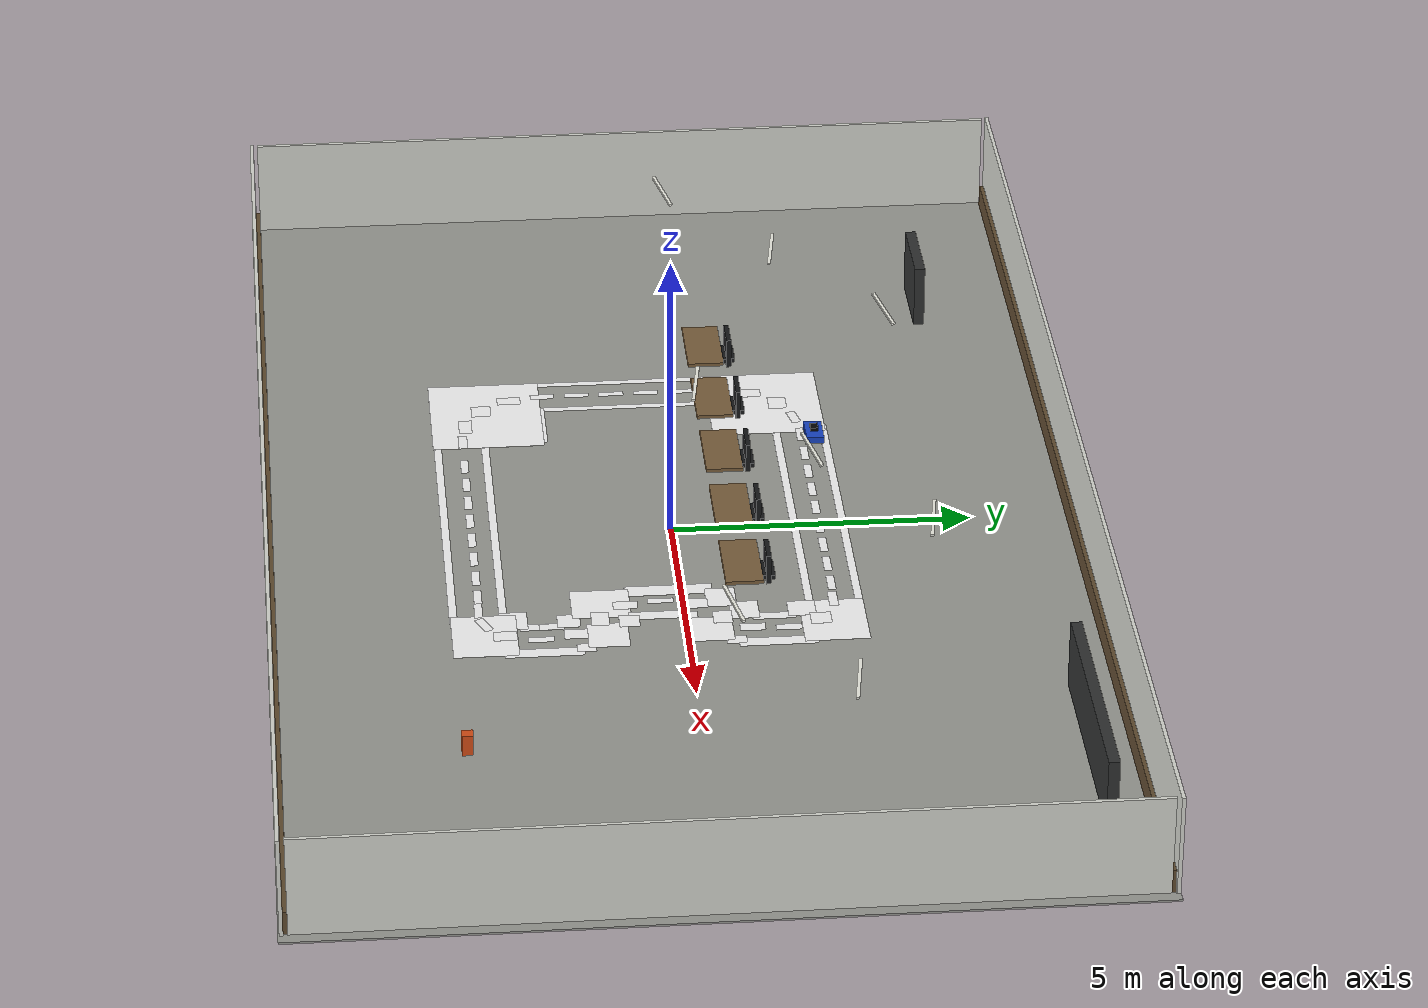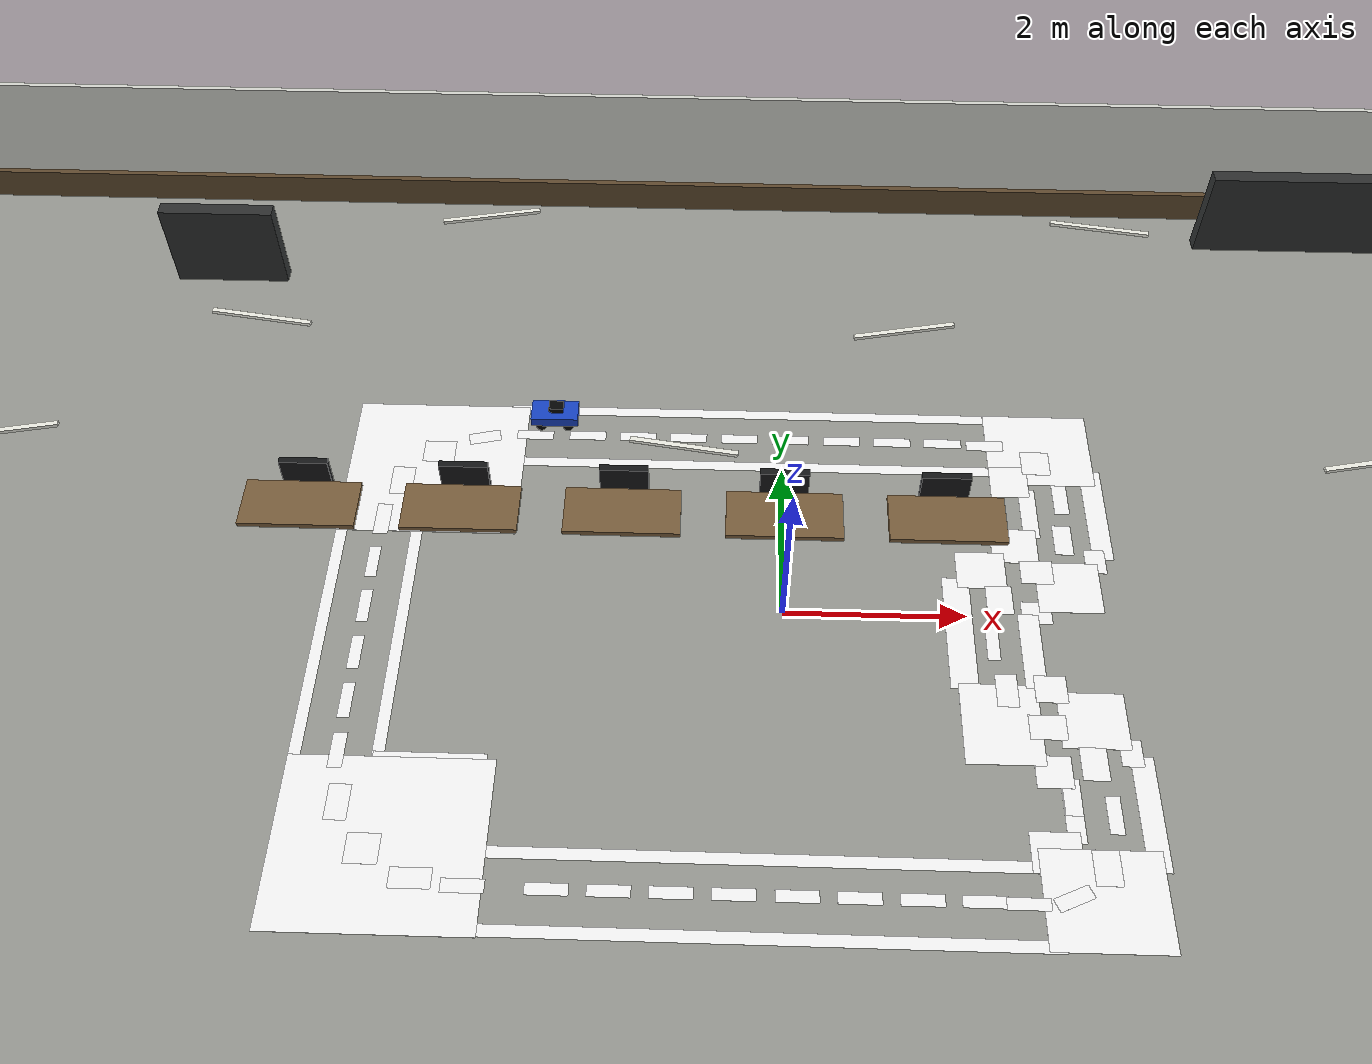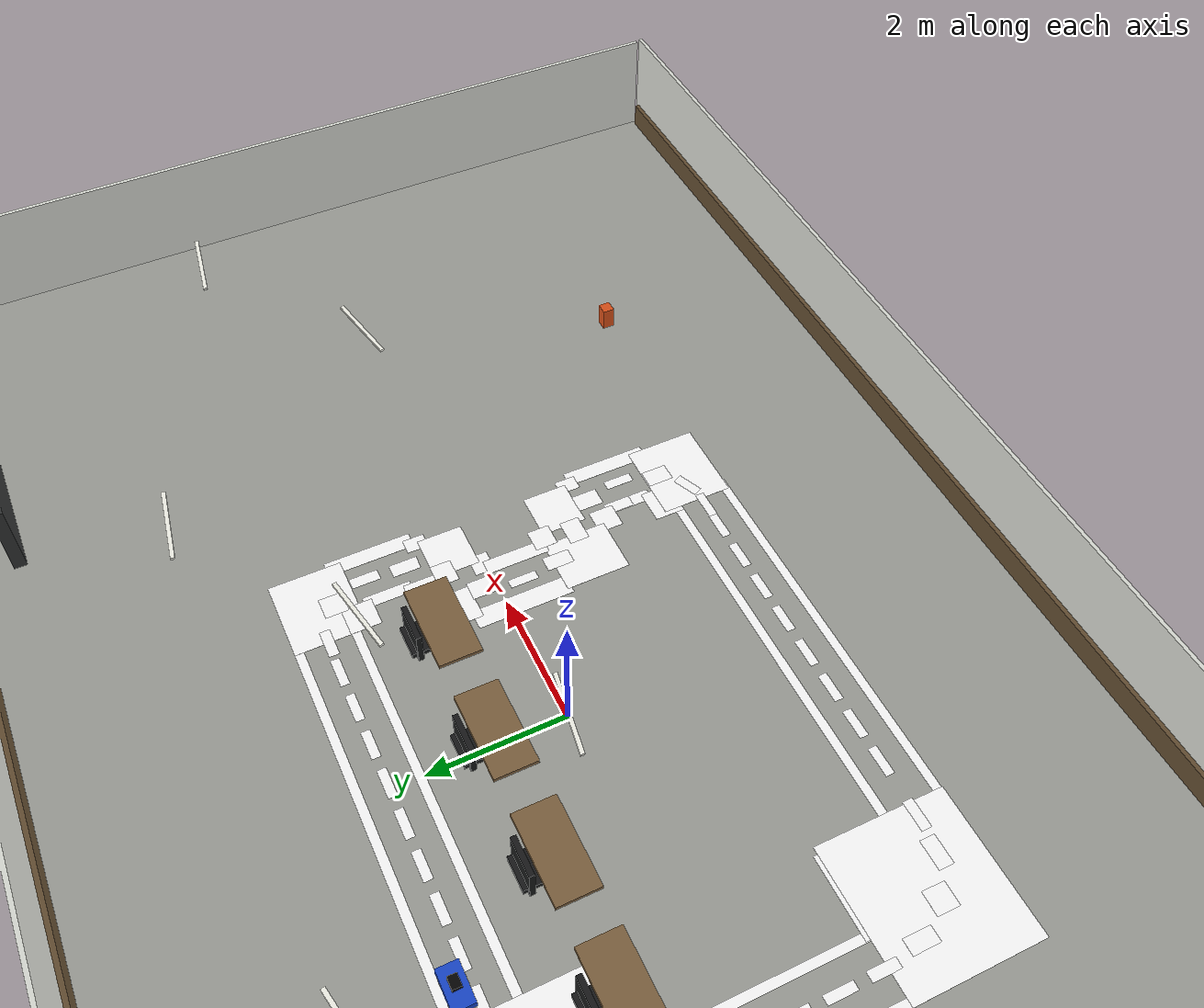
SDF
<sdf version='1.10'>
  <world name='kookmin_xycar_track'>
    <gravity>0 0 -9.8000000000000007</gravity>
    <magnetic_field>6.0000000000000002e-06 2.3e-05 -4.1999999999999998e-05</magnetic_field>
    <atmosphere type='adiabatic'/>
    <physics name='default_physics' default='true' type='ignored'>
      <max_step_size>0.001</max_step_size>
      <real_time_factor>1</real_time_factor>
      <real_time_update_rate>1000</real_time_update_rate>
    </physics>
    <plugin name='gz::sim::systems::Physics' filename='gz-sim-physics-system'/>
    <plugin name='gz::sim::systems::UserCommands' filename='gz-sim-user-commands-system'/>
    <plugin name='gz::sim::systems::SceneBroadcaster' filename='gz-sim-scene-broadcaster-system'/>
    <plugin name='gz::sim::systems::Sensors' filename='gz-sim-sensors-system'>
      <render_engine>ogre2</render_engine>
    </plugin>
    <scene>
      <ambient>0.75 0.75 0.75 1</ambient>
      <background>0.819999993 0.839999974 0.860000014 1</background>
      <shadows>false</shadows>
    </scene>
    <model name='kookmin_track'>
      <static>true</static>
      <pose>0 0 0 0 0 0</pose>
      <link name='floor_base'>
        <pose>0 0 -0.014999999999999999 0 0 0</pose>
        <collision name='collision'>
          <geometry>
            <box>
              <size>22.5 13.5 0.029999999999999999</size>
            </box>
          </geometry>
          <surface>
            <friction>
              <ode>
                <mu>50</mu>
                <mu2>50</mu2>
              </ode>
              <bullet>
                <friction>1</friction>
                <rolling_friction>0.10000000000000001</rolling_friction>
              </bullet>
            </friction>
            <bounce/>
            <contact/>
          </surface>
        </collision>
        <visual name='visual'>
          <geometry>
            <box>
              <size>22.5 13.5 0.029999999999999999</size>
            </box>
          </geometry>
          <material>
            <ambient>0.611800015 0.615700006 0.592199981 1</ambient>
            <diffuse>0.611800015 0.615700006 0.592199981 1</diffuse>
          </material>
        </visual>
        <inertial>
          <pose>0 0 0 0 0 0</pose>
          <mass>1</mass>
          <inertia>
            <ixx>1</ixx>
            <ixy>0</ixy>
            <ixz>0</ixz>
            <iyy>1</iyy>
            <iyz>0</iyz>
            <izz>1</izz>
          </inertia>
        </inertial>
        <enable_wind>false</enable_wind>
      </link>
      <link name='track_texture_surface'>
        <pose>0 0 0.0060000000000000001 0 0 0</pose>
        <visual name='visual'>
          <geometry>
            <plane>
              <normal>0 0 1</normal>
              <size>22.5 13.5</size>
            </plane>
          </geometry>
          <material>
            <ambient>1 1 1 1</ambient>
            <diffuse>1 1 1 1</diffuse>
            <pbr>
              <metal>
                <albedo_map>file://media/materials/textures/kookmin_track_road.png</albedo_map>
                <roughness>1</roughness>
                <metalness>0</metalness>
              </metal>
            </pbr>
          </material>
        </visual>
        <inertial>
          <pose>0 0 0 0 0 0</pose>
          <mass>1</mass>
          <inertia>
            <ixx>1</ixx>
            <ixy>0</ixy>
            <ixz>0</ixz>
            <iyy>1</iyy>
            <iyz>0</iyz>
            <izz>1</izz>
          </inertia>
        </inertial>
        <enable_wind>false</enable_wind>
      </link>
      <self_collide>false</self_collide>
    </model>
    <model name='white_line_cad_01'>
      <static>true</static>
      <pose>-5.0048627853393555 -0.46876698732376099 0.014000000432133675 0 0 0</pose>
      <link name='white_line_cad_01_surface'>
        <visual name='visual'>
          <cast_shadows>false</cast_shadows>
          <geometry>
            <plane>
              <normal>0 0 1</normal>
              <size>0.13 3.1200000000000001</size>
            </plane>
          </geometry>
          <material>
            <ambient>1 1 1 1</ambient>
            <diffuse>1 1 1 1</diffuse>
            <emissive>0.949000001 0.949000001 0.925499976 1</emissive>
            <pbr>
              <metal>
                <albedo_map>file://media/materials/textures/kookmin_white_line_cad_01.png</albedo_map>
                <roughness>1</roughness>
                <metalness>0</metalness>
              </metal>
            </pbr>
          </material>
        </visual>
        <pose>0 0 0 0 0 0</pose>
        <inertial>
          <pose>0 0 0 0 0 0</pose>
          <mass>1</mass>
          <inertia>
            <ixx>1</ixx>
            <ixy>0</ixy>
            <ixz>0</ixz>
            <iyy>1</iyy>
            <iyz>0</iyz>
            <izz>1</izz>
          </inertia>
        </inertial>
        <enable_wind>false</enable_wind>
      </link>
      <self_collide>false</self_collide>
    </model>
    <model name='white_line_cad_02'>
      <static>true</static>
      <pose>-4.1487832069396973 -0.43999999761581421 0.014200000092387199 0 0 0</pose>
      <link name='white_line_cad_02_surface'>
        <visual name='visual'>
          <cast_shadows>false</cast_shadows>
          <geometry>
            <plane>
              <normal>0 0 1</normal>
              <size>0.13 3.1200000000000001</size>
            </plane>
          </geometry>
          <material>
            <ambient>1 1 1 1</ambient>
            <diffuse>1 1 1 1</diffuse>
            <emissive>0.949000001 0.949000001 0.925499976 1</emissive>
            <pbr>
              <metal>
                <albedo_map>file://media/materials/textures/kookmin_white_line_cad_02.png</albedo_map>
                <roughness>1</roughness>
                <metalness>0</metalness>
              </metal>
            </pbr>
          </material>
        </visual>
        <pose>0 0 0 0 0 0</pose>
        <inertial>
          <pose>0 0 0 0 0 0</pose>
          <mass>1</mass>
          <inertia>
            <ixx>1</ixx>
            <ixy>0</ixy>
            <ixz>0</ixz>
            <iyy>1</iyy>
            <iyz>0</iyz>
            <izz>1</izz>
          </inertia>
        </inertial>
        <enable_wind>false</enable_wind>
      </link>
      <self_collide>false</self_collide>
    </model>
    <model name='white_line_cad_03'>
      <static>true</static>
      <pose>-0.22653511166572571 -3.741569995880127 0.014399999752640724 0 0 0</pose>
      <link name='white_line_cad_03_surface'>
        <visual name='visual'>
          <cast_shadows>false</cast_shadows>
          <geometry>
            <plane>
              <normal>0 0 1</normal>
              <size>5.7400000000000002 0.13</size>
            </plane>
          </geometry>
          <material>
            <ambient>1 1 1 1</ambient>
            <diffuse>1 1 1 1</diffuse>
            <emissive>0.949000001 0.949000001 0.925499976 1</emissive>
            <pbr>
              <metal>
                <albedo_map>file://media/materials/textures/kookmin_white_line_cad_03.png</albedo_map>
                <roughness>1</roughness>
                <metalness>0</metalness>
              </metal>
            </pbr>
          </material>
        </visual>
        <pose>0 0 0 0 0 0</pose>
        <inertial>
          <pose>0 0 0 0 0 0</pose>
          <mass>1</mass>
          <inertia>
            <ixx>1</ixx>
            <ixy>0</ixy>
            <ixz>0</ixz>
            <iyy>1</iyy>
            <iyz>0</iyz>
            <izz>1</izz>
          </inertia>
        </inertial>
        <enable_wind>false</enable_wind>
      </link>
      <self_collide>false</self_collide>
    </model>
    <model name='white_line_cad_04'>
      <static>true</static>
      <pose>-0.34999999999999998 -2.9350000000000001 0.0146 0 0 0</pose>
      <link name='white_line_cad_04_surface'>
        <visual name='visual'>
          <cast_shadows>false</cast_shadows>
          <geometry>
            <plane>
              <normal>0 0 1</normal>
              <size>5.7400000000000002 0.13</size>
            </plane>
          </geometry>
          <material>
            <ambient>1 1 1 1</ambient>
            <diffuse>1 1 1 1</diffuse>
            <emissive>0.949000001 0.949000001 0.925499976 1</emissive>
            <pbr>
              <metal>
                <albedo_map>file://media/materials/textures/kookmin_white_line_cad_04.png</albedo_map>
                <roughness>1</roughness>
                <metalness>0</metalness>
              </metal>
            </pbr>
          </material>
        </visual>
        <pose>0 0 0 0 0 0</pose>
        <inertial>
          <pose>0 0 0 0 0 0</pose>
          <mass>1</mass>
          <inertia>
            <ixx>1</ixx>
            <ixy>0</ixy>
            <ixz>0</ixz>
            <iyy>1</iyy>
            <iyz>0</iyz>
            <izz>1</izz>
          </inertia>
        </inertial>
        <enable_wind>false</enable_wind>
      </link>
      <self_collide>false</self_collide>
    </model>
    <model name='white_line_cad_05'>
      <static>true</static>
      <pose>-0.34999999999999998 2.0550000000000002 0.014800000000000001 0 0 0</pose>
      <link name='white_line_cad_05_surface'>
        <visual name='visual'>
          <cast_shadows>false</cast_shadows>
          <geometry>
            <plane>
              <normal>0 0 1</normal>
              <size>5.7800000000000002 0.13</size>
            </plane>
          </geometry>
          <material>
            <ambient>1 1 1 1</ambient>
            <diffuse>1 1 1 1</diffuse>
            <emissive>0.949000001 0.949000001 0.925499976 1</emissive>
            <pbr>
              <metal>
                <albedo_map>file://media/materials/textures/kookmin_white_line_cad_05.png</albedo_map>
                <roughness>1</roughness>
                <metalness>0</metalness>
              </metal>
            </pbr>
          </material>
        </visual>
        <pose>0 0 0 0 0 0</pose>
        <inertial>
          <pose>0 0 0 0 0 0</pose>
          <mass>1</mass>
          <inertia>
            <ixx>1</ixx>
            <ixy>0</ixy>
            <ixz>0</ixz>
            <iyy>1</iyy>
            <iyz>0</iyz>
            <izz>1</izz>
          </inertia>
        </inertial>
        <enable_wind>false</enable_wind>
      </link>
      <self_collide>false</self_collide>
    </model>
    <model name='white_line_cad_06'>
      <static>true</static>
      <pose>-0.34999999999999998 2.8650000000000002 0.014999999999999999 0 0 0</pose>
      <link name='white_line_cad_06_surface'>
        <visual name='visual'>
          <cast_shadows>false</cast_shadows>
          <geometry>
            <plane>
              <normal>0 0 1</normal>
              <size>5.7800000000000002 0.13</size>
            </plane>
          </geometry>
          <material>
            <ambient>1 1 1 1</ambient>
            <diffuse>1 1 1 1</diffuse>
            <emissive>0.949000001 0.949000001 0.925499976 1</emissive>
            <pbr>
              <metal>
                <albedo_map>file://media/materials/textures/kookmin_white_line_cad_06.png</albedo_map>
                <roughness>1</roughness>
                <metalness>0</metalness>
              </metal>
            </pbr>
          </material>
        </visual>
        <pose>0 0 0 0 0 0</pose>
        <inertial>
          <pose>0 0 0 0 0 0</pose>
          <mass>1</mass>
          <inertia>
            <ixx>1</ixx>
            <ixy>0</ixy>
            <ixz>0</ixz>
            <iyy>1</iyy>
            <iyz>0</iyz>
            <izz>1</izz>
          </inertia>
        </inertial>
        <enable_wind>false</enable_wind>
      </link>
      <self_collide>false</self_collide>
    </model>
    <model name='white_line_cad_07'>
      <static>true</static>
      <pose>2.8650000000000002 -2.3149999999999999 0.0152 0 0 0</pose>
      <link name='white_line_cad_07_surface'>
        <visual name='visual'>
          <cast_shadows>false</cast_shadows>
          <geometry>
            <plane>
              <normal>0 0 1</normal>
              <size>0.19 0.70999999999999996</size>
            </plane>
          </geometry>
          <material>
            <ambient>1 1 1 1</ambient>
            <diffuse>1 1 1 1</diffuse>
            <emissive>0.949000001 0.949000001 0.925499976 1</emissive>
            <pbr>
              <metal>
                <albedo_map>file://media/materials/textures/kookmin_white_line_cad_07.png</albedo_map>
                <roughness>1</roughness>
                <metalness>0</metalness>
              </metal>
            </pbr>
          </material>
        </visual>
        <pose>0 0 0 0 0 0</pose>
        <inertial>
          <pose>0 0 0 0 0 0</pose>
          <mass>1</mass>
          <inertia>
            <ixx>1</ixx>
            <ixy>0</ixy>
            <ixz>0</ixz>
            <iyy>1</iyy>
            <iyz>0</iyz>
            <izz>1</izz>
          </inertia>
        </inertial>
        <enable_wind>false</enable_wind>
      </link>
      <self_collide>false</self_collide>
    </model>
    <model name='white_line_cad_08'>
      <static>true</static>
      <pose>2.645 -2.7749999999999999 0.0154 0 0 0</pose>
      <link name='white_line_cad_08_surface'>
        <visual name='visual'>
          <cast_shadows>false</cast_shadows>
          <geometry>
            <plane>
              <normal>0 0 1</normal>
              <size>0.51000000000000001 0.45000000000000001</size>
            </plane>
          </geometry>
          <material>
            <ambient>1 1 1 1</ambient>
            <diffuse>1 1 1 1</diffuse>
            <emissive>0.949000001 0.949000001 0.925499976 1</emissive>
            <pbr>
              <metal>
                <albedo_map>file://media/materials/textures/kookmin_white_line_cad_08.png</albedo_map>
                <roughness>1</roughness>
                <metalness>0</metalness>
              </metal>
            </pbr>
          </material>
        </visual>
        <pose>0 0 0 0 0 0</pose>
        <inertial>
          <pose>0 0 0 0 0 0</pose>
          <mass>1</mass>
          <inertia>
            <ixx>1</ixx>
            <ixy>0</ixy>
            <ixz>0</ixz>
            <iyy>1</iyy>
            <iyz>0</iyz>
            <izz>1</izz>
          </inertia>
        </inertial>
        <enable_wind>false</enable_wind>
      </link>
      <self_collide>false</self_collide>
    </model>
    <model name='white_line_cad_09'>
      <static>true</static>
      <pose>3.0699999999999998 -3.2599999999999998 0.015599999999999999 0 0 0</pose>
      <link name='white_line_cad_09_surface'>
        <visual name='visual'>
          <cast_shadows>false</cast_shadows>
          <geometry>
            <plane>
              <normal>0 0 1</normal>
              <size>1.22 1.0600000000000001</size>
            </plane>
          </geometry>
          <material>
            <ambient>1 1 1 1</ambient>
            <diffuse>1 1 1 1</diffuse>
            <emissive>0.949000001 0.949000001 0.925499976 1</emissive>
            <pbr>
              <metal>
                <albedo_map>file://media/materials/textures/kookmin_white_line_cad_09.png</albedo_map>
                <roughness>1</roughness>
                <metalness>0</metalness>
              </metal>
            </pbr>
          </material>
        </visual>
        <pose>0 0 0 0 0 0</pose>
        <inertial>
          <pose>0 0 0 0 0 0</pose>
          <mass>1</mass>
          <inertia>
            <ixx>1</ixx>
            <ixy>0</ixy>
            <ixz>0</ixz>
            <iyy>1</iyy>
            <iyz>0</iyz>
            <izz>1</izz>
          </inertia>
        </inertial>
        <enable_wind>false</enable_wind>
      </link>
      <self_collide>false</self_collide>
    </model>
    <model name='white_line_cad_10'>
      <static>true</static>
      <pose>3.6299999999999999 -2.3199999999999998 0.015800000000000002 0 0 0</pose>
      <link name='white_line_cad_10_surface'>
        <visual name='visual'>
          <cast_shadows>false</cast_shadows>
          <geometry>
            <plane>
              <normal>0 0 1</normal>
              <size>0.23999999999999999 1.28</size>
            </plane>
          </geometry>
          <material>
            <ambient>1 1 1 1</ambient>
            <diffuse>1 1 1 1</diffuse>
            <emissive>0.949000001 0.949000001 0.925499976 1</emissive>
            <pbr>
              <metal>
                <albedo_map>file://media/materials/textures/kookmin_white_line_cad_10.png</albedo_map>
                <roughness>1</roughness>
                <metalness>0</metalness>
              </metal>
            </pbr>
          </material>
        </visual>
        <pose>0 0 0 0 0 0</pose>
        <inertial>
          <pose>0 0 0 0 0 0</pose>
          <mass>1</mass>
          <inertia>
            <ixx>1</ixx>
            <ixy>0</ixy>
            <ixz>0</ixz>
            <iyy>1</iyy>
            <iyz>0</iyz>
            <izz>1</izz>
          </inertia>
        </inertial>
        <enable_wind>false</enable_wind>
      </link>
      <self_collide>false</self_collide>
    </model>
    <model name='white_line_cad_11'>
      <static>true</static>
      <pose>3.5350000000000001 -1.645 0.016 0 0 0</pose>
      <link name='white_line_cad_11_surface'>
        <visual name='visual'>
          <cast_shadows>false</cast_shadows>
          <geometry>
            <plane>
              <normal>0 0 1</normal>
              <size>0.23000000000000001 0.31</size>
            </plane>
          </geometry>
          <material>
            <ambient>1 1 1 1</ambient>
            <diffuse>1 1 1 1</diffuse>
            <emissive>0.949000001 0.949000001 0.925499976 1</emissive>
            <pbr>
              <metal>
                <albedo_map>file://media/materials/textures/kookmin_white_line_cad_11.png</albedo_map>
                <roughness>1</roughness>
                <metalness>0</metalness>
              </metal>
            </pbr>
          </material>
        </visual>
        <pose>0 0 0 0 0 0</pose>
        <inertial>
          <pose>0 0 0 0 0 0</pose>
          <mass>1</mass>
          <inertia>
            <ixx>1</ixx>
            <ixy>0</ixy>
            <ixz>0</ixz>
            <iyy>1</iyy>
            <iyz>0</iyz>
            <izz>1</izz>
          </inertia>
        </inertial>
        <enable_wind>false</enable_wind>
      </link>
      <self_collide>false</self_collide>
    </model>
    <model name='white_line_cad_12'>
      <static>true</static>
      <pose>2.8149999999999999 1.4450000000000001 0.016199999999999999 0 0 0</pose>
      <link name='white_line_cad_12_surface'>
        <visual name='visual'>
          <cast_shadows>false</cast_shadows>
          <geometry>
            <plane>
              <normal>0 0 1</normal>
              <size>0.19 0.70999999999999996</size>
            </plane>
          </geometry>
          <material>
            <ambient>1 1 1 1</ambient>
            <diffuse>1 1 1 1</diffuse>
            <emissive>0.949000001 0.949000001 0.925499976 1</emissive>
            <pbr>
              <metal>
                <albedo_map>file://media/materials/textures/kookmin_white_line_cad_12.png</albedo_map>
                <roughness>1</roughness>
                <metalness>0</metalness>
              </metal>
            </pbr>
          </material>
        </visual>
        <pose>0 0 0 0 0 0</pose>
        <inertial>
          <pose>0 0 0 0 0 0</pose>
          <mass>1</mass>
          <inertia>
            <ixx>1</ixx>
            <ixy>0</ixy>
            <ixz>0</ixz>
            <iyy>1</iyy>
            <iyz>0</iyz>
            <izz>1</izz>
          </inertia>
        </inertial>
        <enable_wind>false</enable_wind>
      </link>
      <self_collide>false</self_collide>
    </model>
    <model name='white_line_cad_13'>
      <static>true</static>
      <pose>2.6000000000000001 0.97499999999999998 0.016400000000000001 0 0 0</pose>
      <link name='white_line_cad_13_surface'>
        <visual name='visual'>
          <cast_shadows>false</cast_shadows>
          <geometry>
            <plane>
              <normal>0 0 1</normal>
              <size>0.52000000000000002 0.46999999999999997</size>
            </plane>
          </geometry>
          <material>
            <ambient>1 1 1 1</ambient>
            <diffuse>1 1 1 1</diffuse>
            <emissive>0.949000001 0.949000001 0.925499976 1</emissive>
            <pbr>
              <metal>
                <albedo_map>file://media/materials/textures/kookmin_white_line_cad_13.png</albedo_map>
                <roughness>1</roughness>
                <metalness>0</metalness>
              </metal>
            </pbr>
          </material>
        </visual>
        <pose>0 0 0 0 0 0</pose>
        <inertial>
          <pose>0 0 0 0 0 0</pose>
          <mass>1</mass>
          <inertia>
            <ixx>1</ixx>
            <ixy>0</ixy>
            <ixz>0</ixz>
            <iyy>1</iyy>
            <iyz>0</iyz>
            <izz>1</izz>
          </inertia>
        </inertial>
        <enable_wind>false</enable_wind>
      </link>
      <self_collide>false</self_collide>
    </model>
    <model name='white_line_cad_14'>
      <static>true</static>
      <pose>3.02 2.3999999999999999 0.0166 0 0 0</pose>
      <link name='white_line_cad_14_surface'>
        <visual name='visual'>
          <cast_shadows>false</cast_shadows>
          <geometry>
            <plane>
              <normal>0 0 1</normal>
              <size>1.22 1.0600000000000001</size>
            </plane>
          </geometry>
          <material>
            <ambient>1 1 1 1</ambient>
            <diffuse>1 1 1 1</diffuse>
            <emissive>0.949000001 0.949000001 0.925499976 1</emissive>
            <pbr>
              <metal>
                <albedo_map>file://media/materials/textures/kookmin_white_line_cad_14.png</albedo_map>
                <roughness>1</roughness>
                <metalness>0</metalness>
              </metal>
            </pbr>
          </material>
        </visual>
        <pose>0 0 0 0 0 0</pose>
        <inertial>
          <pose>0 0 0 0 0 0</pose>
          <mass>1</mass>
          <inertia>
            <ixx>1</ixx>
            <ixy>0</ixy>
            <ixz>0</ixz>
            <iyy>1</iyy>
            <iyz>0</iyz>
            <izz>1</izz>
          </inertia>
        </inertial>
        <enable_wind>false</enable_wind>
      </link>
      <self_collide>false</self_collide>
    </model>
    <model name='white_line_cad_15'>
      <static>true</static>
      <pose>3.5800000000000001 1.45 0.016799999999999999 0 0 0</pose>
      <link name='white_line_cad_15_surface'>
        <visual name='visual'>
          <cast_shadows>false</cast_shadows>
          <geometry>
            <plane>
              <normal>0 0 1</normal>
              <size>0.23999999999999999 1.28</size>
            </plane>
          </geometry>
          <material>
            <ambient>1 1 1 1</ambient>
            <diffuse>1 1 1 1</diffuse>
            <emissive>0.949000001 0.949000001 0.925499976 1</emissive>
            <pbr>
              <metal>
                <albedo_map>file://media/materials/textures/kookmin_white_line_cad_15.png</albedo_map>
                <roughness>1</roughness>
                <metalness>0</metalness>
              </metal>
            </pbr>
          </material>
        </visual>
        <pose>0 0 0 0 0 0</pose>
        <inertial>
          <pose>0 0 0 0 0 0</pose>
          <mass>1</mass>
          <inertia>
            <ixx>1</ixx>
            <ixy>0</ixy>
            <ixz>0</ixz>
            <iyy>1</iyy>
            <iyz>0</iyz>
            <izz>1</izz>
          </inertia>
        </inertial>
        <enable_wind>false</enable_wind>
      </link>
      <self_collide>false</self_collide>
    </model>
    <model name='white_line_cad_16'>
      <static>true</static>
      <pose>3.4849999999999999 0.78000000000000003 0.017000000000000001 0 0 0</pose>
      <link name='white_line_cad_16_surface'>
        <visual name='visual'>
          <cast_shadows>false</cast_shadows>
          <geometry>
            <plane>
              <normal>0 0 1</normal>
              <size>0.23000000000000001 0.32000000000000001</size>
            </plane>
          </geometry>
          <material>
            <ambient>1 1 1 1</ambient>
            <diffuse>1 1 1 1</diffuse>
            <emissive>0.949000001 0.949000001 0.925499976 1</emissive>
            <pbr>
              <metal>
                <albedo_map>file://media/materials/textures/kookmin_white_line_cad_16.png</albedo_map>
                <roughness>1</roughness>
                <metalness>0</metalness>
              </metal>
            </pbr>
          </material>
        </visual>
        <pose>0 0 0 0 0 0</pose>
        <inertial>
          <pose>0 0 0 0 0 0</pose>
          <mass>1</mass>
          <inertia>
            <ixx>1</ixx>
            <ixy>0</ixy>
            <ixz>0</ixz>
            <iyy>1</iyy>
            <iyz>0</iyz>
            <izz>1</izz>
          </inertia>
        </inertial>
        <enable_wind>false</enable_wind>
      </link>
      <self_collide>false</self_collide>
    </model>
    <model name='white_line_cad_17'>
      <static>true</static>
      <pose>1.8999999999999999 -0.20499999999999999 0.0172 0 0 0</pose>
      <link name='white_line_cad_17_surface'>
        <visual name='visual'>
          <cast_shadows>false</cast_shadows>
          <geometry>
            <plane>
              <normal>0 0 1</normal>
              <size>0.29999999999999999 1.4299999999999999</size>
            </plane>
          </geometry>
          <material>
            <ambient>1 1 1 1</ambient>
            <diffuse>1 1 1 1</diffuse>
            <emissive>0.949000001 0.949000001 0.925499976 1</emissive>
            <pbr>
              <metal>
                <albedo_map>file://media/materials/textures/kookmin_white_line_cad_17.png</albedo_map>
                <roughness>1</roughness>
                <metalness>0</metalness>
              </metal>
            </pbr>
          </material>
        </visual>
        <pose>0 0 0 0 0 0</pose>
        <inertial>
          <pose>0 0 0 0 0 0</pose>
          <mass>1</mass>
          <inertia>
            <ixx>1</ixx>
            <ixy>0</ixy>
            <ixz>0</ixz>
            <iyy>1</iyy>
            <iyz>0</iyz>
            <izz>1</izz>
          </inertia>
        </inertial>
        <enable_wind>false</enable_wind>
      </link>
      <self_collide>false</self_collide>
    </model>
    <model name='white_line_cad_18'>
      <static>true</static>
      <pose>-3.6585278511047363 1.5645300149917603 0.017400000244379044 0 0 0</pose>
      <link name='white_line_cad_18_surface'>
        <visual name='visual'>
          <cast_shadows>false</cast_shadows>
          <geometry>
            <plane>
              <normal>0 0 1</normal>
              <size>1.1399999999999999 1.1299999999999999</size>
            </plane>
          </geometry>
          <material>
            <ambient>1 1 1 1</ambient>
            <diffuse>1 1 1 1</diffuse>
            <emissive>0.949000001 0.949000001 0.925499976 1</emissive>
            <pbr>
              <metal>
                <albedo_map>file://media/materials/textures/kookmin_white_line_cad_18.png</albedo_map>
                <roughness>1</roughness>
                <metalness>0</metalness>
              </metal>
            </pbr>
          </material>
        </visual>
        <pose>0 0 0 0 0 0</pose>
        <inertial>
          <pose>0 0 0 0 0 0</pose>
          <mass>1</mass>
          <inertia>
            <ixx>1</ixx>
            <ixy>0</ixy>
            <ixz>0</ixz>
            <iyy>1</iyy>
            <iyz>0</iyz>
            <izz>1</izz>
          </inertia>
        </inertial>
        <enable_wind>false</enable_wind>
      </link>
      <self_collide>false</self_collide>
    </model>
    <model name='white_line_cad_19'>
      <static>true</static>
      <pose>-4.0487060546875 1.9379400014877319 0.017599999904632568 0 0 0</pose>
      <link name='white_line_cad_19_surface'>
        <visual name='visual'>
          <cast_shadows>false</cast_shadows>
          <geometry>
            <plane>
              <normal>0 0 1</normal>
              <size>2.04 1.9299999999999999</size>
            </plane>
          </geometry>
          <material>
            <ambient>1 1 1 1</ambient>
            <diffuse>1 1 1 1</diffuse>
            <emissive>0.949000001 0.949000001 0.925499976 1</emissive>
            <pbr>
              <metal>
                <albedo_map>file://media/materials/textures/kookmin_white_line_cad_19.png</albedo_map>
                <roughness>1</roughness>
                <metalness>0</metalness>
              </metal>
            </pbr>
          </material>
        </visual>
        <pose>0 0 0 0 0 0</pose>
        <inertial>
          <pose>0 0 0 0 0 0</pose>
          <mass>1</mass>
          <inertia>
            <ixx>1</ixx>
            <ixy>0</ixy>
            <ixz>0</ixz>
            <iyy>1</iyy>
            <iyz>0</iyz>
            <izz>1</izz>
          </inertia>
        </inertial>
        <enable_wind>false</enable_wind>
      </link>
      <self_collide>false</self_collide>
    </model>
    <model name='white_line_cad_20'>
      <static>true</static>
      <pose>-3.6142799854278564 -2.4223885536193848 0.017799999564886093 0 0 0</pose>
      <link name='white_line_cad_20_surface'>
        <visual name='visual'>
          <cast_shadows>false</cast_shadows>
          <geometry>
            <plane>
              <normal>0 0 1</normal>
              <size>1.1699999999999999 1.1299999999999999</size>
            </plane>
          </geometry>
          <material>
            <ambient>1 1 1 1</ambient>
            <diffuse>1 1 1 1</diffuse>
            <emissive>0.949000001 0.949000001 0.925499976 1</emissive>
            <pbr>
              <metal>
                <albedo_map>file://media/materials/textures/kookmin_white_line_cad_20.png</albedo_map>
                <roughness>1</roughness>
                <metalness>0</metalness>
              </metal>
            </pbr>
          </material>
        </visual>
        <pose>0 0 0 0 0 0</pose>
        <inertial>
          <pose>0 0 0 0 0 0</pose>
          <mass>1</mass>
          <inertia>
            <ixx>1</ixx>
            <ixy>0</ixy>
            <ixz>0</ixz>
            <iyy>1</iyy>
            <iyz>0</iyz>
            <izz>1</izz>
          </inertia>
        </inertial>
        <enable_wind>false</enable_wind>
      </link>
      <self_collide>false</self_collide>
    </model>
    <model name='white_line_cad_21'>
      <static>true</static>
      <pose>-3.9988181591033936 -2.8690700531005859 0.017999999225139618 0 0 0</pose>
      <link name='white_line_cad_21_surface'>
        <visual name='visual'>
          <cast_shadows>false</cast_shadows>
          <geometry>
            <plane>
              <normal>0 0 1</normal>
              <size>2.1400000000000001 1.8999999999999999</size>
            </plane>
          </geometry>
          <material>
            <ambient>1 1 1 1</ambient>
            <diffuse>1 1 1 1</diffuse>
            <emissive>0.949000001 0.949000001 0.925499976 1</emissive>
            <pbr>
              <metal>
                <albedo_map>file://media/materials/textures/kookmin_white_line_cad_21.png</albedo_map>
                <roughness>1</roughness>
                <metalness>0</metalness>
              </metal>
            </pbr>
          </material>
        </visual>
        <pose>0 0 0 0 0 0</pose>
        <inertial>
          <pose>0 0 0 0 0 0</pose>
          <mass>1</mass>
          <inertia>
            <ixx>1</ixx>
            <ixy>0</ixy>
            <ixz>0</ixz>
            <iyy>1</iyy>
            <iyz>0</iyz>
            <izz>1</izz>
          </inertia>
        </inertial>
        <enable_wind>false</enable_wind>
      </link>
      <self_collide>false</self_collide>
    </model>
    <model name='white_line_cad_22'>
      <static>true</static>
      <pose>2.8700000000000001 -2.165 0.018200000000000001 0 0 0</pose>
      <link name='white_line_cad_22_surface'>
        <visual name='visual'>
          <cast_shadows>false</cast_shadows>
          <geometry>
            <plane>
              <normal>0 0 1</normal>
              <size>0.17999999999999999 0.40999999999999998</size>
            </plane>
          </geometry>
          <material>
            <ambient>1 1 1 1</ambient>
            <diffuse>1 1 1 1</diffuse>
            <emissive>0.949000001 0.949000001 0.925499976 1</emissive>
            <pbr>
              <metal>
                <albedo_map>file://media/materials/textures/kookmin_white_line_cad_22.png</albedo_map>
                <roughness>1</roughness>
                <metalness>0</metalness>
              </metal>
            </pbr>
          </material>
        </visual>
        <pose>0 0 0 0 0 0</pose>
        <inertial>
          <pose>0 0 0 0 0 0</pose>
          <mass>1</mass>
          <inertia>
            <ixx>1</ixx>
            <ixy>0</ixy>
            <ixz>0</ixz>
            <iyy>1</iyy>
            <iyz>0</iyz>
            <izz>1</izz>
          </inertia>
        </inertial>
        <enable_wind>false</enable_wind>
      </link>
      <self_collide>false</self_collide>
    </model>
    <model name='white_line_cad_23'>
      <static>true</static>
      <pose>2.2450000000000001 -1.3400000000000001 0.0184 0 0 0</pose>
      <link name='white_line_cad_23_surface'>
        <visual name='visual'>
          <cast_shadows>false</cast_shadows>
          <geometry>
            <plane>
              <normal>0 0 1</normal>
              <size>0.82999999999999996 0.95999999999999996</size>
            </plane>
          </geometry>
          <material>
            <ambient>1 1 1 1</ambient>
            <diffuse>1 1 1 1</diffuse>
            <emissive>0.949000001 0.949000001 0.925499976 1</emissive>
            <pbr>
              <metal>
                <albedo_map>file://media/materials/textures/kookmin_white_line_cad_23.png</albedo_map>
                <roughness>1</roughness>
                <metalness>0</metalness>
              </metal>
            </pbr>
          </material>
        </visual>
        <pose>0 0 0 0 0 0</pose>
        <inertial>
          <pose>0 0 0 0 0 0</pose>
          <mass>1</mass>
          <inertia>
            <ixx>1</ixx>
            <ixy>0</ixy>
            <ixz>0</ixz>
            <iyy>1</iyy>
            <iyz>0</iyz>
            <izz>1</izz>
          </inertia>
        </inertial>
        <enable_wind>false</enable_wind>
      </link>
      <self_collide>false</self_collide>
    </model>
    <model name='white_line_cad_24'>
      <static>true</static>
      <pose>2.7200000000000002 -1.885 0.018599999999999998 0 0 0</pose>
      <link name='white_line_cad_24_surface'>
        <visual name='visual'>
          <cast_shadows>false</cast_shadows>
          <geometry>
            <plane>
              <normal>0 0 1</normal>
              <size>0.38 0.37</size>
            </plane>
          </geometry>
          <material>
            <ambient>1 1 1 1</ambient>
            <diffuse>1 1 1 1</diffuse>
            <emissive>0.949000001 0.949000001 0.925499976 1</emissive>
            <pbr>
              <metal>
                <albedo_map>file://media/materials/textures/kookmin_white_line_cad_24.png</albedo_map>
                <roughness>1</roughness>
                <metalness>0</metalness>
              </metal>
            </pbr>
          </material>
        </visual>
        <pose>0 0 0 0 0 0</pose>
        <inertial>
          <pose>0 0 0 0 0 0</pose>
          <mass>1</mass>
          <inertia>
            <ixx>1</ixx>
            <ixy>0</ixy>
            <ixz>0</ixz>
            <iyy>1</iyy>
            <iyz>0</iyz>
            <izz>1</izz>
          </inertia>
        </inertial>
        <enable_wind>false</enable_wind>
      </link>
      <self_collide>false</self_collide>
    </model>
    <model name='white_line_cad_25'>
      <static>true</static>
      <pose>2.1949999999999998 0.625 0.018800000000000001 0 0 0</pose>
      <link name='white_line_cad_25_surface'>
        <visual name='visual'>
          <cast_shadows>false</cast_shadows>
          <geometry>
            <plane>
              <normal>0 0 1</normal>
              <size>0.55000000000000004 0.48999999999999999</size>
            </plane>
          </geometry>
          <material>
            <ambient>1 1 1 1</ambient>
            <diffuse>1 1 1 1</diffuse>
            <emissive>0.949000001 0.949000001 0.925499976 1</emissive>
            <pbr>
              <metal>
                <albedo_map>file://media/materials/textures/kookmin_white_line_cad_25.png</albedo_map>
                <roughness>1</roughness>
                <metalness>0</metalness>
              </metal>
            </pbr>
          </material>
        </visual>
        <pose>0 0 0 0 0 0</pose>
        <inertial>
          <pose>0 0 0 0 0 0</pose>
          <mass>1</mass>
          <inertia>
            <ixx>1</ixx>
            <ixy>0</ixy>
            <ixz>0</ixz>
            <iyy>1</iyy>
            <iyz>0</iyz>
            <izz>1</izz>
          </inertia>
        </inertial>
        <enable_wind>false</enable_wind>
      </link>
      <self_collide>false</self_collide>
    </model>
    <model name='white_line_cad_26'>
      <static>true</static>
      <pose>2.7549999999999999 0.065000000000000002 0.019 0 0 0</pose>
      <link name='white_line_cad_26_surface'>
        <visual name='visual'>
          <cast_shadows>false</cast_shadows>
          <geometry>
            <plane>
              <normal>0 0 1</normal>
              <size>0.33000000000000002 0.28999999999999998</size>
            </plane>
          </geometry>
          <material>
            <ambient>1 1 1 1</ambient>
            <diffuse>1 1 1 1</diffuse>
            <emissive>0.949000001 0.949000001 0.925499976 1</emissive>
            <pbr>
              <metal>
                <albedo_map>file://media/materials/textures/kookmin_white_line_cad_26.png</albedo_map>
                <roughness>1</roughness>
                <metalness>0</metalness>
              </metal>
            </pbr>
          </material>
        </visual>
        <pose>0 0 0 0 0 0</pose>
        <inertial>
          <pose>0 0 0 0 0 0</pose>
          <mass>1</mass>
          <inertia>
            <ixx>1</ixx>
            <ixy>0</ixy>
            <ixz>0</ixz>
            <iyy>1</iyy>
            <iyz>0</iyz>
            <izz>1</izz>
          </inertia>
        </inertial>
        <enable_wind>false</enable_wind>
      </link>
      <self_collide>false</self_collide>
    </model>
    <model name='white_line_cad_27'>
      <static>true</static>
      <pose>3.145 0.41499999999999998 0.019199999999999998 0 0 0</pose>
      <link name='white_line_cad_27_surface'>
        <visual name='visual'>
          <cast_shadows>false</cast_shadows>
          <geometry>
            <plane>
              <normal>0 0 1</normal>
              <size>0.70999999999999996 0.67000000000000004</size>
            </plane>
          </geometry>
          <material>
            <ambient>1 1 1 1</ambient>
            <diffuse>1 1 1 1</diffuse>
            <emissive>0.949000001 0.949000001 0.925499976 1</emissive>
            <pbr>
              <metal>
                <albedo_map>file://media/materials/textures/kookmin_white_line_cad_27.png</albedo_map>
                <roughness>1</roughness>
                <metalness>0</metalness>
              </metal>
            </pbr>
          </material>
        </visual>
        <pose>0 0 0 0 0 0</pose>
        <inertial>
          <pose>0 0 0 0 0 0</pose>
          <mass>1</mass>
          <inertia>
            <ixx>1</ixx>
            <ixy>0</ixy>
            <ixz>0</ixz>
            <iyy>1</iyy>
            <iyz>0</iyz>
            <izz>1</izz>
          </inertia>
        </inertial>
        <enable_wind>false</enable_wind>
      </link>
      <self_collide>false</self_collide>
    </model>
    <model name='white_line_cad_28'>
      <static>true</static>
      <pose>2.6549999999999998 -0.42999999999999999 0.019400000000000001 0 0 0</pose>
      <link name='white_line_cad_28_surface'>
        <visual name='visual'>
          <cast_shadows>false</cast_shadows>
          <geometry>
            <plane>
              <normal>0 0 1</normal>
              <size>0.23000000000000001 0.93999999999999995</size>
            </plane>
          </geometry>
          <material>
            <ambient>1 1 1 1</ambient>
            <diffuse>1 1 1 1</diffuse>
            <emissive>0.949000001 0.949000001 0.925499976 1</emissive>
            <pbr>
              <metal>
                <albedo_map>file://media/materials/textures/kookmin_white_line_cad_28.png</albedo_map>
                <roughness>1</roughness>
                <metalness>0</metalness>
              </metal>
            </pbr>
          </material>
        </visual>
        <pose>0 0 0 0 0 0</pose>
        <inertial>
          <pose>0 0 0 0 0 0</pose>
          <mass>1</mass>
          <inertia>
            <ixx>1</ixx>
            <ixy>0</ixy>
            <ixz>0</ixz>
            <iyy>1</iyy>
            <iyz>0</iyz>
            <izz>1</izz>
          </inertia>
        </inertial>
        <enable_wind>false</enable_wind>
      </link>
      <self_collide>false</self_collide>
    </model>
    <model name='white_line_cad_29'>
      <static>true</static>
      <pose>3.1949999999999998 -1.2749999999999999 0.019599999999999999 0 0 0</pose>
      <link name='white_line_cad_29_surface'>
        <visual name='visual'>
          <cast_shadows>false</cast_shadows>
          <geometry>
            <plane>
              <normal>0 0 1</normal>
              <size>0.70999999999999996 0.67000000000000004</size>
            </plane>
          </geometry>
          <material>
            <ambient>1 1 1 1</ambient>
            <diffuse>1 1 1 1</diffuse>
            <emissive>0.949000001 0.949000001 0.925499976 1</emissive>
            <pbr>
              <metal>
                <albedo_map>file://media/materials/textures/kookmin_white_line_cad_29.png</albedo_map>
                <roughness>1</roughness>
                <metalness>0</metalness>
              </metal>
            </pbr>
          </material>
        </visual>
        <pose>0 0 0 0 0 0</pose>
        <inertial>
          <pose>0 0 0 0 0 0</pose>
          <mass>1</mass>
          <inertia>
            <ixx>1</ixx>
            <ixy>0</ixy>
            <ixz>0</ixz>
            <iyy>1</iyy>
            <iyz>0</iyz>
            <izz>1</izz>
          </inertia>
        </inertial>
        <enable_wind>false</enable_wind>
      </link>
      <self_collide>false</self_collide>
    </model>
    <model name='white_line_cad_30'>
      <static>true</static>
      <pose>2.7999999999999998 -0.90500000000000003 0.019800000000000002 0 0 0</pose>
      <link name='white_line_cad_30_surface'>
        <visual name='visual'>
          <cast_shadows>false</cast_shadows>
          <geometry>
            <plane>
              <normal>0 0 1</normal>
              <size>0.34000000000000002 0.33000000000000002</size>
            </plane>
          </geometry>
          <material>
            <ambient>1 1 1 1</ambient>
            <diffuse>1 1 1 1</diffuse>
            <emissive>0.949000001 0.949000001 0.925499976 1</emissive>
            <pbr>
              <metal>
                <albedo_map>file://media/materials/textures/kookmin_white_line_cad_30.png</albedo_map>
                <roughness>1</roughness>
                <metalness>0</metalness>
              </metal>
            </pbr>
          </material>
        </visual>
        <pose>0 0 0 0 0 0</pose>
        <inertial>
          <pose>0 0 0 0 0 0</pose>
          <mass>1</mass>
          <inertia>
            <ixx>1</ixx>
            <ixy>0</ixy>
            <ixz>0</ixz>
            <iyy>1</iyy>
            <iyz>0</iyz>
            <izz>1</izz>
          </inertia>
        </inertial>
        <enable_wind>false</enable_wind>
      </link>
      <self_collide>false</self_collide>
    </model>
    <model name='white_line_cad_31'>
      <static>true</static>
      <pose>2.6299999999999999 1.905 0.02 0 0 0</pose>
      <link name='white_line_cad_31_surface'>
        <visual name='visual'>
          <cast_shadows>false</cast_shadows>
          <geometry>
            <plane>
              <normal>0 0 1</normal>
              <size>0.44 0.45000000000000001</size>
            </plane>
          </geometry>
          <material>
            <ambient>1 1 1 1</ambient>
            <diffuse>1 1 1 1</diffuse>
            <emissive>0.949000001 0.949000001 0.925499976 1</emissive>
            <pbr>
              <metal>
                <albedo_map>file://media/materials/textures/kookmin_white_line_cad_31.png</albedo_map>
                <roughness>1</roughness>
                <metalness>0</metalness>
              </metal>
            </pbr>
          </material>
        </visual>
        <pose>0 0 0 0 0 0</pose>
        <inertial>
          <pose>0 0 0 0 0 0</pose>
          <mass>1</mass>
          <inertia>
            <ixx>1</ixx>
            <ixy>0</ixy>
            <ixz>0</ixz>
            <iyy>1</iyy>
            <iyz>0</iyz>
            <izz>1</izz>
          </inertia>
        </inertial>
        <enable_wind>false</enable_wind>
      </link>
      <self_collide>false</self_collide>
    </model>
    <model name='yellow_centerline_dash_001'>
      <static>true</static>
      <pose>-2.3050000000000002 2.4649999999999999 0.026499999999999999 0 0 0</pose>
      <link name='yellow_centerline_dash_001_surface'>
        <visual name='visual'>
          <cast_shadows>false</cast_shadows>
          <geometry>
            <plane>
              <normal>0 0 1</normal>
              <size>0.42999999999999999 0.13</size>
            </plane>
          </geometry>
          <material>
            <ambient>1 1 1 1</ambient>
            <diffuse>1 1 1 1</diffuse>
            <emissive>1 0.768599987 0.0471000001 1</emissive>
            <pbr>
              <metal>
                <albedo_map>file://media/materials/textures/kookmin_yellow_centerline_dash_001.png</albedo_map>
                <roughness>1</roughness>
                <metalness>0</metalness>
              </metal>
            </pbr>
          </material>
        </visual>
        <pose>0 0 0 0 0 0</pose>
        <inertial>
          <pose>0 0 0 0 0 0</pose>
          <mass>1</mass>
          <inertia>
            <ixx>1</ixx>
            <ixy>0</ixy>
            <ixz>0</ixz>
            <iyy>1</iyy>
            <iyz>0</iyz>
            <izz>1</izz>
          </inertia>
        </inertial>
        <enable_wind>false</enable_wind>
      </link>
      <self_collide>false</self_collide>
    </model>
    <model name='yellow_centerline_dash_002'>
      <static>true</static>
      <pose>-1.7050000000000001 2.4649999999999999 0.026700000000000002 0 0 0</pose>
      <link name='yellow_centerline_dash_002_surface'>
        <visual name='visual'>
          <cast_shadows>false</cast_shadows>
          <geometry>
            <plane>
              <normal>0 0 1</normal>
              <size>0.42999999999999999 0.13</size>
            </plane>
          </geometry>
          <material>
            <ambient>1 1 1 1</ambient>
            <diffuse>1 1 1 1</diffuse>
            <emissive>1 0.768599987 0.0471000001 1</emissive>
            <pbr>
              <metal>
                <albedo_map>file://media/materials/textures/kookmin_yellow_centerline_dash_002.png</albedo_map>
                <roughness>1</roughness>
                <metalness>0</metalness>
              </metal>
            </pbr>
          </material>
        </visual>
        <pose>0 0 0 0 0 0</pose>
        <inertial>
          <pose>0 0 0 0 0 0</pose>
          <mass>1</mass>
          <inertia>
            <ixx>1</ixx>
            <ixy>0</ixy>
            <ixz>0</ixz>
            <iyy>1</iyy>
            <iyz>0</iyz>
            <izz>1</izz>
          </inertia>
        </inertial>
        <enable_wind>false</enable_wind>
      </link>
      <self_collide>false</self_collide>
    </model>
    <model name='yellow_centerline_dash_003'>
      <static>true</static>
      <pose>-1.105 2.4649999999999999 0.0269 0 0 0</pose>
      <link name='yellow_centerline_dash_003_surface'>
        <visual name='visual'>
          <cast_shadows>false</cast_shadows>
          <geometry>
            <plane>
              <normal>0 0 1</normal>
              <size>0.42999999999999999 0.13</size>
            </plane>
          </geometry>
          <material>
            <ambient>1 1 1 1</ambient>
            <diffuse>1 1 1 1</diffuse>
            <emissive>1 0.768599987 0.0471000001 1</emissive>
            <pbr>
              <metal>
                <albedo_map>file://media/materials/textures/kookmin_yellow_centerline_dash_003.png</albedo_map>
                <roughness>1</roughness>
                <metalness>0</metalness>
              </metal>
            </pbr>
          </material>
        </visual>
        <pose>0 0 0 0 0 0</pose>
        <inertial>
          <pose>0 0 0 0 0 0</pose>
          <mass>1</mass>
          <inertia>
            <ixx>1</ixx>
            <ixy>0</ixy>
            <ixz>0</ixz>
            <iyy>1</iyy>
            <iyz>0</iyz>
            <izz>1</izz>
          </inertia>
        </inertial>
        <enable_wind>false</enable_wind>
      </link>
      <self_collide>false</self_collide>
    </model>
    <model name='yellow_centerline_dash_004'>
      <static>true</static>
      <pose>-0.505 2.4649999999999999 0.027099999999999999 0 0 0</pose>
      <link name='yellow_centerline_dash_004_surface'>
        <visual name='visual'>
          <cast_shadows>false</cast_shadows>
          <geometry>
            <plane>
              <normal>0 0 1</normal>
              <size>0.42999999999999999 0.13</size>
            </plane>
          </geometry>
          <material>
            <ambient>1 1 1 1</ambient>
            <diffuse>1 1 1 1</diffuse>
            <emissive>1 0.768599987 0.0471000001 1</emissive>
            <pbr>
              <metal>
                <albedo_map>file://media/materials/textures/kookmin_yellow_centerline_dash_004.png</albedo_map>
                <roughness>1</roughness>
                <metalness>0</metalness>
              </metal>
            </pbr>
          </material>
        </visual>
        <pose>0 0 0 0 0 0</pose>
        <inertial>
          <pose>0 0 0 0 0 0</pose>
          <mass>1</mass>
          <inertia>
            <ixx>1</ixx>
            <ixy>0</ixy>
            <ixz>0</ixz>
            <iyy>1</iyy>
            <iyz>0</iyz>
            <izz>1</izz>
          </inertia>
        </inertial>
        <enable_wind>false</enable_wind>
      </link>
      <self_collide>false</self_collide>
    </model>
    <model name='yellow_centerline_dash_005'>
      <static>true</static>
      <pose>0.105 2.4649999999999999 0.027300000000000001 0 0 0</pose>
      <link name='yellow_centerline_dash_005_surface'>
        <visual name='visual'>
          <cast_shadows>false</cast_shadows>
          <geometry>
            <plane>
              <normal>0 0 1</normal>
              <size>0.42999999999999999 0.13</size>
            </plane>
          </geometry>
          <material>
            <ambient>1 1 1 1</ambient>
            <diffuse>1 1 1 1</diffuse>
            <emissive>1 0.768599987 0.0471000001 1</emissive>
            <pbr>
              <metal>
                <albedo_map>file://media/materials/textures/kookmin_yellow_centerline_dash_005.png</albedo_map>
                <roughness>1</roughness>
                <metalness>0</metalness>
              </metal>
            </pbr>
          </material>
        </visual>
        <pose>0 0 0 0 0 0</pose>
        <inertial>
          <pose>0 0 0 0 0 0</pose>
          <mass>1</mass>
          <inertia>
            <ixx>1</ixx>
            <ixy>0</ixy>
            <ixz>0</ixz>
            <iyy>1</iyy>
            <iyz>0</iyz>
            <izz>1</izz>
          </inertia>
        </inertial>
        <enable_wind>false</enable_wind>
      </link>
      <self_collide>false</self_collide>
    </model>
    <model name='yellow_centerline_dash_006'>
      <static>true</static>
      <pose>0.70499999999999996 2.4649999999999999 0.0275 0 0 0</pose>
      <link name='yellow_centerline_dash_006_surface'>
        <visual name='visual'>
          <cast_shadows>false</cast_shadows>
          <geometry>
            <plane>
              <normal>0 0 1</normal>
              <size>0.42999999999999999 0.13</size>
            </plane>
          </geometry>
          <material>
            <ambient>1 1 1 1</ambient>
            <diffuse>1 1 1 1</diffuse>
            <emissive>1 0.768599987 0.0471000001 1</emissive>
            <pbr>
              <metal>
                <albedo_map>file://media/materials/textures/kookmin_yellow_centerline_dash_006.png</albedo_map>
                <roughness>1</roughness>
                <metalness>0</metalness>
              </metal>
            </pbr>
          </material>
        </visual>
        <pose>0 0 0 0 0 0</pose>
        <inertial>
          <pose>0 0 0 0 0 0</pose>
          <mass>1</mass>
          <inertia>
            <ixx>1</ixx>
            <ixy>0</ixy>
            <ixz>0</ixz>
            <iyy>1</iyy>
            <iyz>0</iyz>
            <izz>1</izz>
          </inertia>
        </inertial>
        <enable_wind>false</enable_wind>
      </link>
      <self_collide>false</self_collide>
    </model>
    <model name='yellow_centerline_dash_007'>
      <static>true</static>
      <pose>1.3049999999999999 2.4649999999999999 0.027699999999999999 0 0 0</pose>
      <link name='yellow_centerline_dash_007_surface'>
        <visual name='visual'>
          <cast_shadows>false</cast_shadows>
          <geometry>
            <plane>
              <normal>0 0 1</normal>
              <size>0.42999999999999999 0.13</size>
            </plane>
          </geometry>
          <material>
            <ambient>1 1 1 1</ambient>
            <diffuse>1 1 1 1</diffuse>
            <emissive>1 0.768599987 0.0471000001 1</emissive>
            <pbr>
              <metal>
                <albedo_map>file://media/materials/textures/kookmin_yellow_centerline_dash_007.png</albedo_map>
                <roughness>1</roughness>
                <metalness>0</metalness>
              </metal>
            </pbr>
          </material>
        </visual>
        <pose>0 0 0 0 0 0</pose>
        <inertial>
          <pose>0 0 0 0 0 0</pose>
          <mass>1</mass>
          <inertia>
            <ixx>1</ixx>
            <ixy>0</ixy>
            <ixz>0</ixz>
            <iyy>1</iyy>
            <iyz>0</iyz>
            <izz>1</izz>
          </inertia>
        </inertial>
        <enable_wind>false</enable_wind>
      </link>
      <self_collide>false</self_collide>
    </model>
    <model name='yellow_centerline_dash_008'>
      <static>true</static>
      <pose>1.8999999999999999 2.4649999999999999 0.027900000000000001 0 0 0</pose>
      <link name='yellow_centerline_dash_008_surface'>
        <visual name='visual'>
          <cast_shadows>false</cast_shadows>
          <geometry>
            <plane>
              <normal>0 0 1</normal>
              <size>0.44 0.13</size>
            </plane>
          </geometry>
          <material>
            <ambient>1 1 1 1</ambient>
            <diffuse>1 1 1 1</diffuse>
            <emissive>1 0.768599987 0.0471000001 1</emissive>
            <pbr>
              <metal>
                <albedo_map>file://media/materials/textures/kookmin_yellow_centerline_dash_008.png</albedo_map>
                <roughness>1</roughness>
                <metalness>0</metalness>
              </metal>
            </pbr>
          </material>
        </visual>
        <pose>0 0 0 0 0 0</pose>
        <inertial>
          <pose>0 0 0 0 0 0</pose>
          <mass>1</mass>
          <inertia>
            <ixx>1</ixx>
            <ixy>0</ixy>
            <ixz>0</ixz>
            <iyy>1</iyy>
            <iyz>0</iyz>
            <izz>1</izz>
          </inertia>
        </inertial>
        <enable_wind>false</enable_wind>
      </link>
      <self_collide>false</self_collide>
    </model>
    <model name='yellow_centerline_dash_009'>
      <static>true</static>
      <pose>-2.928236722946167 2.4549999237060547 0.028100000694394112 0 0 0</pose>
      <link name='yellow_centerline_dash_009_surface'>
        <visual name='visual'>
          <cast_shadows>false</cast_shadows>
          <geometry>
            <plane>
              <normal>0 0 1</normal>
              <size>0.42999999999999999 0.13</size>
            </plane>
          </geometry>
          <material>
            <ambient>1 1 1 1</ambient>
            <diffuse>1 1 1 1</diffuse>
            <emissive>1 0.768599987 0.0471000001 1</emissive>
            <pbr>
              <metal>
                <albedo_map>file://media/materials/textures/kookmin_yellow_centerline_dash_009.png</albedo_map>
                <roughness>1</roughness>
                <metalness>0</metalness>
              </metal>
            </pbr>
          </material>
        </visual>
        <pose>0 0 0 0 0 0</pose>
        <inertial>
          <pose>0 0 0 0 0 0</pose>
          <mass>1</mass>
          <inertia>
            <ixx>1</ixx>
            <ixy>0</ixy>
            <ixz>0</ixz>
            <iyy>1</iyy>
            <iyz>0</iyz>
            <izz>1</izz>
          </inertia>
        </inertial>
        <enable_wind>false</enable_wind>
      </link>
      <self_collide>false</self_collide>
    </model>
    <model name='yellow_centerline_dash_010'>
      <static>true</static>
      <pose>2.395 2.4449999999999998 0.028299999999999999 0 0 0</pose>
      <link name='yellow_centerline_dash_010_surface'>
        <visual name='visual'>
          <cast_shadows>false</cast_shadows>
          <geometry>
            <plane>
              <normal>0 0 1</normal>
              <size>0.42999999999999999 0.14999999999999999</size>
            </plane>
          </geometry>
          <material>
            <ambient>1 1 1 1</ambient>
            <diffuse>1 1 1 1</diffuse>
            <emissive>1 0.768599987 0.0471000001 1</emissive>
            <pbr>
              <metal>
                <albedo_map>file://media/materials/textures/kookmin_yellow_centerline_dash_010.png</albedo_map>
                <roughness>1</roughness>
                <metalness>0</metalness>
              </metal>
            </pbr>
          </material>
        </visual>
        <pose>0 0 0 0 0 0</pose>
        <inertial>
          <pose>0 0 0 0 0 0</pose>
          <mass>1</mass>
          <inertia>
            <ixx>1</ixx>
            <ixy>0</ixy>
            <ixz>0</ixz>
            <iyy>1</iyy>
            <iyz>0</iyz>
            <izz>1</izz>
          </inertia>
        </inertial>
        <enable_wind>false</enable_wind>
      </link>
      <self_collide>false</self_collide>
    </model>
    <model name='yellow_centerline_dash_011'>
      <static>true</static>
      <pose>-3.5250000953674316 2.4000000953674316 0.028500000014901161 0 0 0.22944573427692086</pose>
      <link name='yellow_centerline_dash_011_surface'>
        <visual name='visual'>
          <cast_shadows>false</cast_shadows>
          <geometry>
            <plane>
              <normal>0 0 1</normal>
              <size>0.37 0.16</size>
            </plane>
          </geometry>
          <material>
            <ambient>1 1 1 1</ambient>
            <diffuse>1 1 1 1</diffuse>
            <emissive>1 0.768599987 0.0471000001 1</emissive>
            <pbr>
              <metal>
                <albedo_map>file://media/materials/textures/kookmin_yellow_centerline_dash_011.png</albedo_map>
                <roughness>1</roughness>
                <metalness>0</metalness>
              </metal>
            </pbr>
          </material>
        </visual>
        <pose>0 0 0 0 0 0</pose>
        <inertial>
          <pose>0 0 0 0 0 0</pose>
          <mass>1</mass>
          <inertia>
            <ixx>1</ixx>
            <ixy>0</ixy>
            <ixz>0</ixz>
            <iyy>1</iyy>
            <iyz>0</iyz>
            <izz>1</izz>
          </inertia>
        </inertial>
        <enable_wind>false</enable_wind>
      </link>
      <self_collide>false</self_collide>
    </model>
    <model name='yellow_centerline_dash_012'>
      <static>true</static>
      <pose>2.9649999999999999 2.1899999999999999 0.0287 0 0 0</pose>
      <link name='yellow_centerline_dash_012_surface'>
        <visual name='visual'>
          <cast_shadows>false</cast_shadows>
          <geometry>
            <plane>
              <normal>0 0 1</normal>
              <size>0.33000000000000002 0.34000000000000002</size>
            </plane>
          </geometry>
          <material>
            <ambient>1 1 1 1</ambient>
            <diffuse>1 1 1 1</diffuse>
            <emissive>1 0.768599987 0.0471000001 1</emissive>
            <pbr>
              <metal>
                <albedo_map>file://media/materials/textures/kookmin_yellow_centerline_dash_012.png</albedo_map>
                <roughness>1</roughness>
                <metalness>0</metalness>
              </metal>
            </pbr>
          </material>
        </visual>
        <pose>0 0 0 0 0 0</pose>
        <inertial>
          <pose>0 0 0 0 0 0</pose>
          <mass>1</mass>
          <inertia>
            <ixx>1</ixx>
            <ixy>0</ixy>
            <ixz>0</ixz>
            <iyy>1</iyy>
            <iyz>0</iyz>
            <izz>1</izz>
          </inertia>
        </inertial>
        <enable_wind>false</enable_wind>
      </link>
      <self_collide>false</self_collide>
    </model>
    <model name='yellow_centerline_dash_013'>
      <static>true</static>
      <pose>-4.0350000000000001 2.165 0.028899999999999999 0 0 0</pose>
      <link name='yellow_centerline_dash_013_surface'>
        <visual name='visual'>
          <cast_shadows>false</cast_shadows>
          <geometry>
            <plane>
              <normal>0 0 1</normal>
              <size>0.37 0.31</size>
            </plane>
          </geometry>
          <material>
            <ambient>1 1 1 1</ambient>
            <diffuse>1 1 1 1</diffuse>
            <emissive>1 0.768599987 0.0471000001 1</emissive>
            <pbr>
              <metal>
                <albedo_map>file://media/materials/textures/kookmin_yellow_centerline_dash_013.png</albedo_map>
                <roughness>1</roughness>
                <metalness>0</metalness>
              </metal>
            </pbr>
          </material>
        </visual>
        <pose>0 0 0 0 0 0</pose>
        <inertial>
          <pose>0 0 0 0 0 0</pose>
          <mass>1</mass>
          <inertia>
            <ixx>1</ixx>
            <ixy>0</ixy>
            <ixz>0</ixz>
            <iyy>1</iyy>
            <iyz>0</iyz>
            <izz>1</izz>
          </inertia>
        </inertial>
        <enable_wind>false</enable_wind>
      </link>
      <self_collide>false</self_collide>
    </model>
    <model name='yellow_centerline_dash_014'>
      <static>true</static>
      <pose>-4.4100000000000001 1.71 0.029100000000000001 0 0 0</pose>
      <link name='yellow_centerline_dash_014_surface'>
        <visual name='visual'>
          <cast_shadows>false</cast_shadows>
          <geometry>
            <plane>
              <normal>0 0 1</normal>
              <size>0.26000000000000001 0.40000000000000002</size>
            </plane>
          </geometry>
          <material>
            <ambient>1 1 1 1</ambient>
            <diffuse>1 1 1 1</diffuse>
            <emissive>1 0.768599987 0.0471000001 1</emissive>
            <pbr>
              <metal>
                <albedo_map>file://media/materials/textures/kookmin_yellow_centerline_dash_014.png</albedo_map>
                <roughness>1</roughness>
                <metalness>0</metalness>
              </metal>
            </pbr>
          </material>
        </visual>
        <pose>0 0 0 0 0 0</pose>
        <inertial>
          <pose>0 0 0 0 0 0</pose>
          <mass>1</mass>
          <inertia>
            <ixx>1</ixx>
            <ixy>0</ixy>
            <ixz>0</ixz>
            <iyy>1</iyy>
            <iyz>0</iyz>
            <izz>1</izz>
          </inertia>
        </inertial>
        <enable_wind>false</enable_wind>
      </link>
      <self_collide>false</self_collide>
    </model>
    <model name='yellow_centerline_dash_015'>
      <static>true</static>
      <pose>3.1949999999999998 1.6499999999999999 0.0293 0 0 0</pose>
      <link name='yellow_centerline_dash_015_surface'>
        <visual name='visual'>
          <cast_shadows>false</cast_shadows>
          <geometry>
            <plane>
              <normal>0 0 1</normal>
              <size>0.17000000000000001 0.41999999999999998</size>
            </plane>
          </geometry>
          <material>
            <ambient>1 1 1 1</ambient>
            <diffuse>1 1 1 1</diffuse>
            <emissive>1 0.768599987 0.0471000001 1</emissive>
            <pbr>
              <metal>
                <albedo_map>file://media/materials/textures/kookmin_yellow_centerline_dash_015.png</albedo_map>
                <roughness>1</roughness>
                <metalness>0</metalness>
              </metal>
            </pbr>
          </material>
        </visual>
        <pose>0 0 0 0 0 0</pose>
        <inertial>
          <pose>0 0 0 0 0 0</pose>
          <mass>1</mass>
          <inertia>
            <ixx>1</ixx>
            <ixy>0</ixy>
            <ixz>0</ixz>
            <iyy>1</iyy>
            <iyz>0</iyz>
            <izz>1</izz>
          </inertia>
        </inertial>
        <enable_wind>false</enable_wind>
      </link>
      <self_collide>false</self_collide>
    </model>
    <model name='yellow_centerline_dash_016'>
      <static>true</static>
      <pose>-4.5549999999999997 1.135 0.029499999999999998 0 0 0</pose>
      <link name='yellow_centerline_dash_016_surface'>
        <visual name='visual'>
          <cast_shadows>false</cast_shadows>
          <geometry>
            <plane>
              <normal>0 0 1</normal>
              <size>0.17000000000000001 0.42999999999999999</size>
            </plane>
          </geometry>
          <material>
            <ambient>1 1 1 1</ambient>
            <diffuse>1 1 1 1</diffuse>
            <emissive>1 0.768599987 0.0471000001 1</emissive>
            <pbr>
              <metal>
                <albedo_map>file://media/materials/textures/kookmin_yellow_centerline_dash_016.png</albedo_map>
                <roughness>1</roughness>
                <metalness>0</metalness>
              </metal>
            </pbr>
          </material>
        </visual>
        <pose>0 0 0 0 0 0</pose>
        <inertial>
          <pose>0 0 0 0 0 0</pose>
          <mass>1</mass>
          <inertia>
            <ixx>1</ixx>
            <ixy>0</ixy>
            <ixz>0</ixz>
            <iyy>1</iyy>
            <iyz>0</iyz>
            <izz>1</izz>
          </inertia>
        </inertial>
        <enable_wind>false</enable_wind>
      </link>
      <self_collide>false</self_collide>
    </model>
    <model name='yellow_centerline_dash_017'>
      <static>true</static>
      <pose>3.1549999999999998 1.0649999999999999 0.029700000000000001 0 0 0</pose>
      <link name='yellow_centerline_dash_017_surface'>
        <visual name='visual'>
          <cast_shadows>false</cast_shadows>
          <geometry>
            <plane>
              <normal>0 0 1</normal>
              <size>0.20999999999999999 0.40999999999999998</size>
            </plane>
          </geometry>
          <material>
            <ambient>1 1 1 1</ambient>
            <diffuse>1 1 1 1</diffuse>
            <emissive>1 0.768599987 0.0471000001 1</emissive>
            <pbr>
              <metal>
                <albedo_map>file://media/materials/textures/kookmin_yellow_centerline_dash_017.png</albedo_map>
                <roughness>1</roughness>
                <metalness>0</metalness>
              </metal>
            </pbr>
          </material>
        </visual>
        <pose>0 0 0 0 0 0</pose>
        <inertial>
          <pose>0 0 0 0 0 0</pose>
          <mass>1</mass>
          <inertia>
            <ixx>1</ixx>
            <ixy>0</ixy>
            <ixz>0</ixz>
            <iyy>1</iyy>
            <iyz>0</iyz>
            <izz>1</izz>
          </inertia>
        </inertial>
        <enable_wind>false</enable_wind>
      </link>
      <self_collide>false</self_collide>
    </model>
    <model name='yellow_centerline_dash_018'>
      <static>true</static>
      <pose>2.8100000000000001 0.60499999999999998 0.029899999999999999 0 0 0</pose>
      <link name='yellow_centerline_dash_018_surface'>
        <visual name='visual'>
          <cast_shadows>false</cast_shadows>
          <geometry>
            <plane>
              <normal>0 0 1</normal>
              <size>0.35999999999999999 0.31</size>
            </plane>
          </geometry>
          <material>
            <ambient>1 1 1 1</ambient>
            <diffuse>1 1 1 1</diffuse>
            <emissive>1 0.768599987 0.0471000001 1</emissive>
            <pbr>
              <metal>
                <albedo_map>file://media/materials/textures/kookmin_yellow_centerline_dash_018.png</albedo_map>
                <roughness>1</roughness>
                <metalness>0</metalness>
              </metal>
            </pbr>
          </material>
        </visual>
        <pose>0 0 0 0 0 0</pose>
        <inertial>
          <pose>0 0 0 0 0 0</pose>
          <mass>1</mass>
          <inertia>
            <ixx>1</ixx>
            <ixy>0</ixy>
            <ixz>0</ixz>
            <iyy>1</iyy>
            <iyz>0</iyz>
            <izz>1</izz>
          </inertia>
        </inertial>
        <enable_wind>false</enable_wind>
      </link>
      <self_collide>false</self_collide>
    </model>
    <model name='yellow_centerline_dash_019'>
      <static>true</static>
      <pose>-4.5750000000000002 0.53000000000000003 0.030099999999999998 0 0 0</pose>
      <link name='yellow_centerline_dash_019_surface'>
        <visual name='visual'>
          <cast_shadows>false</cast_shadows>
          <geometry>
            <plane>
              <normal>0 0 1</normal>
              <size>0.13 0.41999999999999998</size>
            </plane>
          </geometry>
          <material>
            <ambient>1 1 1 1</ambient>
            <diffuse>1 1 1 1</diffuse>
            <emissive>1 0.768599987 0.0471000001 1</emissive>
            <pbr>
              <metal>
                <albedo_map>file://media/materials/textures/kookmin_yellow_centerline_dash_019.png</albedo_map>
                <roughness>1</roughness>
                <metalness>0</metalness>
              </metal>
            </pbr>
          </material>
        </visual>
        <pose>0 0 0 0 0 0</pose>
        <inertial>
          <pose>0 0 0 0 0 0</pose>
          <mass>1</mass>
          <inertia>
            <ixx>1</ixx>
            <ixy>0</ixy>
            <ixz>0</ixz>
            <iyy>1</iyy>
            <iyz>0</iyz>
            <izz>1</izz>
          </inertia>
        </inertial>
        <enable_wind>false</enable_wind>
      </link>
      <self_collide>false</self_collide>
    </model>
    <model name='yellow_centerline_dash_020'>
      <static>true</static>
      <pose>2.3650000000000002 0.215 0.030300000000000001 0 0 0</pose>
      <link name='yellow_centerline_dash_020_surface'>
        <visual name='visual'>
          <cast_shadows>false</cast_shadows>
          <geometry>
            <plane>
              <normal>0 0 1</normal>
              <size>0.28999999999999998 0.37</size>
            </plane>
          </geometry>
          <material>
            <ambient>1 1 1 1</ambient>
            <diffuse>1 1 1 1</diffuse>
            <emissive>1 0.768599987 0.0471000001 1</emissive>
            <pbr>
              <metal>
                <albedo_map>file://media/materials/textures/kookmin_yellow_centerline_dash_020.png</albedo_map>
                <roughness>1</roughness>
                <metalness>0</metalness>
              </metal>
            </pbr>
          </material>
        </visual>
        <pose>0 0 0 0 0 0</pose>
        <inertial>
          <pose>0 0 0 0 0 0</pose>
          <mass>1</mass>
          <inertia>
            <ixx>1</ixx>
            <ixy>0</ixy>
            <ixz>0</ixz>
            <iyy>1</iyy>
            <iyz>0</iyz>
            <izz>1</izz>
          </inertia>
        </inertial>
        <enable_wind>false</enable_wind>
      </link>
      <self_collide>false</self_collide>
    </model>
    <model name='yellow_centerline_dash_021'>
      <static>true</static>
      <pose>-4.5750000000000002 -0.070000000000000007 0.030499999999999999 0 0 0</pose>
      <link name='yellow_centerline_dash_021_surface'>
        <visual name='visual'>
          <cast_shadows>false</cast_shadows>
          <geometry>
            <plane>
              <normal>0 0 1</normal>
              <size>0.13 0.41999999999999998</size>
            </plane>
          </geometry>
          <material>
            <ambient>1 1 1 1</ambient>
            <diffuse>1 1 1 1</diffuse>
            <emissive>1 0.768599987 0.0471000001 1</emissive>
            <pbr>
              <metal>
                <albedo_map>file://media/materials/textures/kookmin_yellow_centerline_dash_021.png</albedo_map>
                <roughness>1</roughness>
                <metalness>0</metalness>
              </metal>
            </pbr>
          </material>
        </visual>
        <pose>0 0 0 0 0 0</pose>
        <inertial>
          <pose>0 0 0 0 0 0</pose>
          <mass>1</mass>
          <inertia>
            <ixx>1</ixx>
            <ixy>0</ixy>
            <ixz>0</ixz>
            <iyy>1</iyy>
            <iyz>0</iyz>
            <izz>1</izz>
          </inertia>
        </inertial>
        <enable_wind>false</enable_wind>
      </link>
      <self_collide>false</self_collide>
    </model>
    <model name='yellow_centerline_dash_022'>
      <static>true</static>
      <pose>2.2400000000000002 -0.35999999999999999 0.030700000000000002 0 0 0</pose>
      <link name='yellow_centerline_dash_022_surface'>
        <visual name='visual'>
          <cast_shadows>false</cast_shadows>
          <geometry>
            <plane>
              <normal>0 0 1</normal>
              <size>0.14000000000000001 0.41999999999999998</size>
            </plane>
          </geometry>
          <material>
            <ambient>1 1 1 1</ambient>
            <diffuse>1 1 1 1</diffuse>
            <emissive>1 0.768599987 0.0471000001 1</emissive>
            <pbr>
              <metal>
                <albedo_map>file://media/materials/textures/kookmin_yellow_centerline_dash_022.png</albedo_map>
                <roughness>1</roughness>
                <metalness>0</metalness>
              </metal>
            </pbr>
          </material>
        </visual>
        <pose>0 0 0 0 0 0</pose>
        <inertial>
          <pose>0 0 0 0 0 0</pose>
          <mass>1</mass>
          <inertia>
            <ixx>1</ixx>
            <ixy>0</ixy>
            <ixz>0</ixz>
            <iyy>1</iyy>
            <iyz>0</iyz>
            <izz>1</izz>
          </inertia>
        </inertial>
        <enable_wind>false</enable_wind>
      </link>
      <self_collide>false</self_collide>
    </model>
    <model name='yellow_centerline_dash_023'>
      <static>true</static>
      <pose>-4.5750000000000002 -0.67000000000000004 0.0309 0 0 0</pose>
      <link name='yellow_centerline_dash_023_surface'>
        <visual name='visual'>
          <cast_shadows>false</cast_shadows>
          <geometry>
            <plane>
              <normal>0 0 1</normal>
              <size>0.13 0.41999999999999998</size>
            </plane>
          </geometry>
          <material>
            <ambient>1 1 1 1</ambient>
            <diffuse>1 1 1 1</diffuse>
            <emissive>1 0.768599987 0.0471000001 1</emissive>
            <pbr>
              <metal>
                <albedo_map>file://media/materials/textures/kookmin_yellow_centerline_dash_023.png</albedo_map>
                <roughness>1</roughness>
                <metalness>0</metalness>
              </metal>
            </pbr>
          </material>
        </visual>
        <pose>0 0 0 0 0 0</pose>
        <inertial>
          <pose>0 0 0 0 0 0</pose>
          <mass>1</mass>
          <inertia>
            <ixx>1</ixx>
            <ixy>0</ixy>
            <ixz>0</ixz>
            <iyy>1</iyy>
            <iyz>0</iyz>
            <izz>1</izz>
          </inertia>
        </inertial>
        <enable_wind>false</enable_wind>
      </link>
      <self_collide>false</self_collide>
    </model>
    <model name='yellow_centerline_dash_024'>
      <static>true</static>
      <pose>2.335 -0.93999999999999995 0.031099999999999999 0 0 0</pose>
      <link name='yellow_centerline_dash_024_surface'>
        <visual name='visual'>
          <cast_shadows>false</cast_shadows>
          <geometry>
            <plane>
              <normal>0 0 1</normal>
              <size>0.23000000000000001 0.40000000000000002</size>
            </plane>
          </geometry>
          <material>
            <ambient>1 1 1 1</ambient>
            <diffuse>1 1 1 1</diffuse>
            <emissive>1 0.768599987 0.0471000001 1</emissive>
            <pbr>
              <metal>
                <albedo_map>file://media/materials/textures/kookmin_yellow_centerline_dash_024.png</albedo_map>
                <roughness>1</roughness>
                <metalness>0</metalness>
              </metal>
            </pbr>
          </material>
        </visual>
        <pose>0 0 0 0 0 0</pose>
        <inertial>
          <pose>0 0 0 0 0 0</pose>
          <mass>1</mass>
          <inertia>
            <ixx>1</ixx>
            <ixy>0</ixy>
            <ixz>0</ixz>
            <iyy>1</iyy>
            <iyz>0</iyz>
            <izz>1</izz>
          </inertia>
        </inertial>
        <enable_wind>false</enable_wind>
      </link>
      <self_collide>false</self_collide>
    </model>
    <model name='yellow_centerline_dash_025'>
      <static>true</static>
      <pose>-4.5750000000000002 -1.27 0.031300000000000001 0 0 0</pose>
      <link name='yellow_centerline_dash_025_surface'>
        <visual name='visual'>
          <cast_shadows>false</cast_shadows>
          <geometry>
            <plane>
              <normal>0 0 1</normal>
              <size>0.13 0.41999999999999998</size>
            </plane>
          </geometry>
          <material>
            <ambient>1 1 1 1</ambient>
            <diffuse>1 1 1 1</diffuse>
            <emissive>1 0.768599987 0.0471000001 1</emissive>
            <pbr>
              <metal>
                <albedo_map>file://media/materials/textures/kookmin_yellow_centerline_dash_025.png</albedo_map>
                <roughness>1</roughness>
                <metalness>0</metalness>
              </metal>
            </pbr>
          </material>
        </visual>
        <pose>0 0 0 0 0 0</pose>
        <inertial>
          <pose>0 0 0 0 0 0</pose>
          <mass>1</mass>
          <inertia>
            <ixx>1</ixx>
            <ixy>0</ixy>
            <ixz>0</ixz>
            <iyy>1</iyy>
            <iyz>0</iyz>
            <izz>1</izz>
          </inertia>
        </inertial>
        <enable_wind>false</enable_wind>
      </link>
      <self_collide>false</self_collide>
    </model>
    <model name='yellow_centerline_dash_026'>
      <static>true</static>
      <pose>2.7149999999999999 -1.375 0.0315 0 0 0</pose>
      <link name='yellow_centerline_dash_026_surface'>
        <visual name='visual'>
          <cast_shadows>false</cast_shadows>
          <geometry>
            <plane>
              <normal>0 0 1</normal>
              <size>0.39000000000000001 0.28999999999999998</size>
            </plane>
          </geometry>
          <material>
            <ambient>1 1 1 1</ambient>
            <diffuse>1 1 1 1</diffuse>
            <emissive>1 0.768599987 0.0471000001 1</emissive>
            <pbr>
              <metal>
                <albedo_map>file://media/materials/textures/kookmin_yellow_centerline_dash_026.png</albedo_map>
                <roughness>1</roughness>
                <metalness>0</metalness>
              </metal>
            </pbr>
          </material>
        </visual>
        <pose>0 0 0 0 0 0</pose>
        <inertial>
          <pose>0 0 0 0 0 0</pose>
          <mass>1</mass>
          <inertia>
            <ixx>1</ixx>
            <ixy>0</ixy>
            <ixz>0</ixz>
            <iyy>1</iyy>
            <iyz>0</iyz>
            <izz>1</izz>
          </inertia>
        </inertial>
        <enable_wind>false</enable_wind>
      </link>
      <self_collide>false</self_collide>
    </model>
    <model name='yellow_centerline_dash_027'>
      <static>true</static>
      <pose>3.1400000000000001 -1.79 0.031699999999999999 0 0 0</pose>
      <link name='yellow_centerline_dash_027_surface'>
        <visual name='visual'>
          <cast_shadows>false</cast_shadows>
          <geometry>
            <plane>
              <normal>0 0 1</normal>
              <size>0.28000000000000003 0.38</size>
            </plane>
          </geometry>
          <material>
            <ambient>1 1 1 1</ambient>
            <diffuse>1 1 1 1</diffuse>
            <emissive>1 0.768599987 0.0471000001 1</emissive>
            <pbr>
              <metal>
                <albedo_map>file://media/materials/textures/kookmin_yellow_centerline_dash_027.png</albedo_map>
                <roughness>1</roughness>
                <metalness>0</metalness>
              </metal>
            </pbr>
          </material>
        </visual>
        <pose>0 0 0 0 0 0</pose>
        <inertial>
          <pose>0 0 0 0 0 0</pose>
          <mass>1</mass>
          <inertia>
            <ixx>1</ixx>
            <ixy>0</ixy>
            <ixz>0</ixz>
            <iyy>1</iyy>
            <iyz>0</iyz>
            <izz>1</izz>
          </inertia>
        </inertial>
        <enable_wind>false</enable_wind>
      </link>
      <self_collide>false</self_collide>
    </model>
    <model name='yellow_centerline_dash_028'>
      <static>true</static>
      <pose>-4.5650000000000004 -1.865 0.031899999999999998 0 0 0</pose>
      <link name='yellow_centerline_dash_028_surface'>
        <visual name='visual'>
          <cast_shadows>false</cast_shadows>
          <geometry>
            <plane>
              <normal>0 0 1</normal>
              <size>0.14999999999999999 0.40999999999999998</size>
            </plane>
          </geometry>
          <material>
            <ambient>1 1 1 1</ambient>
            <diffuse>1 1 1 1</diffuse>
            <emissive>1 0.768599987 0.0471000001 1</emissive>
            <pbr>
              <metal>
                <albedo_map>file://media/materials/textures/kookmin_yellow_centerline_dash_028.png</albedo_map>
                <roughness>1</roughness>
                <metalness>0</metalness>
              </metal>
            </pbr>
          </material>
        </visual>
        <pose>0 0 0 0 0 0</pose>
        <inertial>
          <pose>0 0 0 0 0 0</pose>
          <mass>1</mass>
          <inertia>
            <ixx>1</ixx>
            <ixy>0</ixy>
            <ixz>0</ixz>
            <iyy>1</iyy>
            <iyz>0</iyz>
            <izz>1</izz>
          </inertia>
        </inertial>
        <enable_wind>false</enable_wind>
      </link>
      <self_collide>false</self_collide>
    </model>
    <model name='yellow_centerline_dash_029'>
      <static>true</static>
      <pose>3.2650000000000001 -2.3599999999999999 0.032099999999999997 0 0 0</pose>
      <link name='yellow_centerline_dash_029_surface'>
        <visual name='visual'>
          <cast_shadows>false</cast_shadows>
          <geometry>
            <plane>
              <normal>0 0 1</normal>
              <size>0.14999999999999999 0.41999999999999998</size>
            </plane>
          </geometry>
          <material>
            <ambient>1 1 1 1</ambient>
            <diffuse>1 1 1 1</diffuse>
            <emissive>1 0.768599987 0.0471000001 1</emissive>
            <pbr>
              <metal>
                <albedo_map>file://media/materials/textures/kookmin_yellow_centerline_dash_029.png</albedo_map>
                <roughness>1</roughness>
                <metalness>0</metalness>
              </metal>
            </pbr>
          </material>
        </visual>
        <pose>0 0 0 0 0 0</pose>
        <inertial>
          <pose>0 0 0 0 0 0</pose>
          <mass>1</mass>
          <inertia>
            <ixx>1</ixx>
            <ixy>0</ixy>
            <ixz>0</ixz>
            <iyy>1</iyy>
            <iyz>0</iyz>
            <izz>1</izz>
          </inertia>
        </inertial>
        <enable_wind>false</enable_wind>
      </link>
      <self_collide>false</self_collide>
    </model>
    <model name='yellow_centerline_dash_030'>
      <static>true</static>
      <pose>-4.4649999999999999 -2.4500000000000002 0.032300000000000002 0 0 0</pose>
      <link name='yellow_centerline_dash_030_surface'>
        <visual name='visual'>
          <cast_shadows>false</cast_shadows>
          <geometry>
            <plane>
              <normal>0 0 1</normal>
              <size>0.23000000000000001 0.40000000000000002</size>
            </plane>
          </geometry>
          <material>
            <ambient>1 1 1 1</ambient>
            <diffuse>1 1 1 1</diffuse>
            <emissive>1 0.768599987 0.0471000001 1</emissive>
            <pbr>
              <metal>
                <albedo_map>file://media/materials/textures/kookmin_yellow_centerline_dash_030.png</albedo_map>
                <roughness>1</roughness>
                <metalness>0</metalness>
              </metal>
            </pbr>
          </material>
        </visual>
        <pose>0 0 0 0 0 0</pose>
        <inertial>
          <pose>0 0 0 0 0 0</pose>
          <mass>1</mass>
          <inertia>
            <ixx>1</ixx>
            <ixy>0</ixy>
            <ixz>0</ixz>
            <iyy>1</iyy>
            <iyz>0</iyz>
            <izz>1</izz>
          </inertia>
        </inertial>
        <enable_wind>false</enable_wind>
      </link>
      <self_collide>false</self_collide>
    </model>
    <model name='yellow_centerline_dash_031'>
      <static>true</static>
      <pose>3.1150000000000002 -2.9300000000000002 0.032500000000000001 0 0 0</pose>
      <link name='yellow_centerline_dash_031_surface'>
        <visual name='visual'>
          <cast_shadows>false</cast_shadows>
          <geometry>
            <plane>
              <normal>0 0 1</normal>
              <size>0.27000000000000002 0.38</size>
            </plane>
          </geometry>
          <material>
            <ambient>1 1 1 1</ambient>
            <diffuse>1 1 1 1</diffuse>
            <emissive>1 0.768599987 0.0471000001 1</emissive>
            <pbr>
              <metal>
                <albedo_map>file://media/materials/textures/kookmin_yellow_centerline_dash_031.png</albedo_map>
                <roughness>1</roughness>
                <metalness>0</metalness>
              </metal>
            </pbr>
          </material>
        </visual>
        <pose>0 0 0 0 0 0</pose>
        <inertial>
          <pose>0 0 0 0 0 0</pose>
          <mass>1</mass>
          <inertia>
            <ixx>1</ixx>
            <ixy>0</ixy>
            <ixz>0</ixz>
            <iyy>1</iyy>
            <iyz>0</iyz>
            <izz>1</izz>
          </inertia>
        </inertial>
        <enable_wind>false</enable_wind>
      </link>
      <self_collide>false</self_collide>
    </model>
    <model name='yellow_centerline_dash_032'>
      <static>true</static>
      <pose>-4.1399999999999997 -2.9449999999999998 0.0327 0 0 0</pose>
      <link name='yellow_centerline_dash_032_surface'>
        <visual name='visual'>
          <cast_shadows>false</cast_shadows>
          <geometry>
            <plane>
              <normal>0 0 1</normal>
              <size>0.34000000000000002 0.33000000000000002</size>
            </plane>
          </geometry>
          <material>
            <ambient>1 1 1 1</ambient>
            <diffuse>1 1 1 1</diffuse>
            <emissive>1 0.768599987 0.0471000001 1</emissive>
            <pbr>
              <metal>
                <albedo_map>file://media/materials/textures/kookmin_yellow_centerline_dash_032.png</albedo_map>
                <roughness>1</roughness>
                <metalness>0</metalness>
              </metal>
            </pbr>
          </material>
        </visual>
        <pose>0 0 0 0 0 0</pose>
        <inertial>
          <pose>0 0 0 0 0 0</pose>
          <mass>1</mass>
          <inertia>
            <ixx>1</ixx>
            <ixy>0</ixy>
            <ixz>0</ixz>
            <iyy>1</iyy>
            <iyz>0</iyz>
            <izz>1</izz>
          </inertia>
        </inertial>
        <enable_wind>false</enable_wind>
      </link>
      <self_collide>false</self_collide>
    </model>
    <model name='yellow_centerline_dash_033'>
      <static>true</static>
      <pose>-3.6299999999999999 -3.2400000000000002 0.032899999999999999 0 0 0</pose>
      <link name='yellow_centerline_dash_033_surface'>
        <visual name='visual'>
          <cast_shadows>false</cast_shadows>
          <geometry>
            <plane>
              <normal>0 0 1</normal>
              <size>0.41999999999999998 0.22</size>
            </plane>
          </geometry>
          <material>
            <ambient>1 1 1 1</ambient>
            <diffuse>1 1 1 1</diffuse>
            <emissive>1 0.768599987 0.0471000001 1</emissive>
            <pbr>
              <metal>
                <albedo_map>file://media/materials/textures/kookmin_yellow_centerline_dash_033.png</albedo_map>
                <roughness>1</roughness>
                <metalness>0</metalness>
              </metal>
            </pbr>
          </material>
        </visual>
        <pose>0 0 0 0 0 0</pose>
        <inertial>
          <pose>0 0 0 0 0 0</pose>
          <mass>1</mass>
          <inertia>
            <ixx>1</ixx>
            <ixy>0</ixy>
            <ixz>0</ixz>
            <iyy>1</iyy>
            <iyz>0</iyz>
            <izz>1</izz>
          </inertia>
        </inertial>
        <enable_wind>false</enable_wind>
      </link>
      <self_collide>false</self_collide>
    </model>
    <model name='yellow_centerline_dash_034'>
      <static>true</static>
      <pose>2.7546629905700684 -3.2555220127105713 0.033100001513957977 0 0 0.42480900877644706</pose>
      <link name='yellow_centerline_dash_034_surface'>
        <visual name='visual'>
          <cast_shadows>false</cast_shadows>
          <geometry>
            <plane>
              <normal>0 0 1</normal>
              <size>0.39000000000000001 0.14999999999999999</size>
            </plane>
          </geometry>
          <material>
            <ambient>1 1 1 1</ambient>
            <diffuse>1 1 1 1</diffuse>
            <emissive>1 0.768599987 0.0471000001 1</emissive>
            <pbr>
              <metal>
                <albedo_map>file://media/materials/textures/kookmin_yellow_centerline_dash_034.png</albedo_map>
                <roughness>1</roughness>
                <metalness>0</metalness>
              </metal>
            </pbr>
          </material>
        </visual>
        <pose>0 0 0 0 0 0</pose>
        <inertial>
          <pose>0 0 0 0 0 0</pose>
          <mass>1</mass>
          <inertia>
            <ixx>1</ixx>
            <ixy>0</ixy>
            <ixz>0</ixz>
            <iyy>1</iyy>
            <iyz>0</iyz>
            <izz>1</izz>
          </inertia>
        </inertial>
        <enable_wind>false</enable_wind>
      </link>
      <self_collide>false</self_collide>
    </model>
    <model name='yellow_centerline_dash_035'>
      <static>true</static>
      <pose>-3.1150000000000002 -3.3050000000000002 0.033300000000000003 0 0 0</pose>
      <link name='yellow_centerline_dash_035_surface'>
        <visual name='visual'>
          <cast_shadows>false</cast_shadows>
          <geometry>
            <plane>
              <normal>0 0 1</normal>
              <size>0.42999999999999999 0.14999999999999999</size>
            </plane>
          </geometry>
          <material>
            <ambient>1 1 1 1</ambient>
            <diffuse>1 1 1 1</diffuse>
            <emissive>1 0.768599987 0.0471000001 1</emissive>
            <pbr>
              <metal>
                <albedo_map>file://media/materials/textures/kookmin_yellow_centerline_dash_035.png</albedo_map>
                <roughness>1</roughness>
                <metalness>0</metalness>
              </metal>
            </pbr>
          </material>
        </visual>
        <pose>0 0 0 0 0 0</pose>
        <inertial>
          <pose>0 0 0 0 0 0</pose>
          <mass>1</mass>
          <inertia>
            <ixx>1</ixx>
            <ixy>0</ixy>
            <ixz>0</ixz>
            <iyy>1</iyy>
            <iyz>0</iyz>
            <izz>1</izz>
          </inertia>
        </inertial>
        <enable_wind>false</enable_wind>
      </link>
      <self_collide>false</self_collide>
    </model>
    <model name='yellow_centerline_dash_036'>
      <static>true</static>
      <pose>-2.3050000000000002 -3.3149999999999999 0.033500000000000002 0 0 0</pose>
      <link name='yellow_centerline_dash_036_surface'>
        <visual name='visual'>
          <cast_shadows>false</cast_shadows>
          <geometry>
            <plane>
              <normal>0 0 1</normal>
              <size>0.42999999999999999 0.13</size>
            </plane>
          </geometry>
          <material>
            <ambient>1 1 1 1</ambient>
            <diffuse>1 1 1 1</diffuse>
            <emissive>1 0.768599987 0.0471000001 1</emissive>
            <pbr>
              <metal>
                <albedo_map>file://media/materials/textures/kookmin_yellow_centerline_dash_036.png</albedo_map>
                <roughness>1</roughness>
                <metalness>0</metalness>
              </metal>
            </pbr>
          </material>
        </visual>
        <pose>0 0 0 0 0 0</pose>
        <inertial>
          <pose>0 0 0 0 0 0</pose>
          <mass>1</mass>
          <inertia>
            <ixx>1</ixx>
            <ixy>0</ixy>
            <ixz>0</ixz>
            <iyy>1</iyy>
            <iyz>0</iyz>
            <izz>1</izz>
          </inertia>
        </inertial>
        <enable_wind>false</enable_wind>
      </link>
      <self_collide>false</self_collide>
    </model>
    <model name='yellow_centerline_dash_037'>
      <static>true</static>
      <pose>-1.7050000000000001 -3.3149999999999999 0.033700000000000001 0 0 0</pose>
      <link name='yellow_centerline_dash_037_surface'>
        <visual name='visual'>
          <cast_shadows>false</cast_shadows>
          <geometry>
            <plane>
              <normal>0 0 1</normal>
              <size>0.42999999999999999 0.13</size>
            </plane>
          </geometry>
          <material>
            <ambient>1 1 1 1</ambient>
            <diffuse>1 1 1 1</diffuse>
            <emissive>1 0.768599987 0.0471000001 1</emissive>
            <pbr>
              <metal>
                <albedo_map>file://media/materials/textures/kookmin_yellow_centerline_dash_037.png</albedo_map>
                <roughness>1</roughness>
                <metalness>0</metalness>
              </metal>
            </pbr>
          </material>
        </visual>
        <pose>0 0 0 0 0 0</pose>
        <inertial>
          <pose>0 0 0 0 0 0</pose>
          <mass>1</mass>
          <inertia>
            <ixx>1</ixx>
            <ixy>0</ixy>
            <ixz>0</ixz>
            <iyy>1</iyy>
            <iyz>0</iyz>
            <izz>1</izz>
          </inertia>
        </inertial>
        <enable_wind>false</enable_wind>
      </link>
      <self_collide>false</self_collide>
    </model>
    <model name='yellow_centerline_dash_038'>
      <static>true</static>
      <pose>-1.105 -3.3149999999999999 0.0339 0 0 0</pose>
      <link name='yellow_centerline_dash_038_surface'>
        <visual name='visual'>
          <cast_shadows>false</cast_shadows>
          <geometry>
            <plane>
              <normal>0 0 1</normal>
              <size>0.42999999999999999 0.13</size>
            </plane>
          </geometry>
          <material>
            <ambient>1 1 1 1</ambient>
            <diffuse>1 1 1 1</diffuse>
            <emissive>1 0.768599987 0.0471000001 1</emissive>
            <pbr>
              <metal>
                <albedo_map>file://media/materials/textures/kookmin_yellow_centerline_dash_038.png</albedo_map>
                <roughness>1</roughness>
                <metalness>0</metalness>
              </metal>
            </pbr>
          </material>
        </visual>
        <pose>0 0 0 0 0 0</pose>
        <inertial>
          <pose>0 0 0 0 0 0</pose>
          <mass>1</mass>
          <inertia>
            <ixx>1</ixx>
            <ixy>0</ixy>
            <ixz>0</ixz>
            <iyy>1</iyy>
            <iyz>0</iyz>
            <izz>1</izz>
          </inertia>
        </inertial>
        <enable_wind>false</enable_wind>
      </link>
      <self_collide>false</self_collide>
    </model>
    <model name='yellow_centerline_dash_039'>
      <static>true</static>
      <pose>-0.505 -3.3149999999999999 0.034099999999999998 0 0 0</pose>
      <link name='yellow_centerline_dash_039_surface'>
        <visual name='visual'>
          <cast_shadows>false</cast_shadows>
          <geometry>
            <plane>
              <normal>0 0 1</normal>
              <size>0.42999999999999999 0.13</size>
            </plane>
          </geometry>
          <material>
            <ambient>1 1 1 1</ambient>
            <diffuse>1 1 1 1</diffuse>
            <emissive>1 0.768599987 0.0471000001 1</emissive>
            <pbr>
              <metal>
                <albedo_map>file://media/materials/textures/kookmin_yellow_centerline_dash_039.png</albedo_map>
                <roughness>1</roughness>
                <metalness>0</metalness>
              </metal>
            </pbr>
          </material>
        </visual>
        <pose>0 0 0 0 0 0</pose>
        <inertial>
          <pose>0 0 0 0 0 0</pose>
          <mass>1</mass>
          <inertia>
            <ixx>1</ixx>
            <ixy>0</ixy>
            <ixz>0</ixz>
            <iyy>1</iyy>
            <iyz>0</iyz>
            <izz>1</izz>
          </inertia>
        </inertial>
        <enable_wind>false</enable_wind>
      </link>
      <self_collide>false</self_collide>
    </model>
    <model name='yellow_centerline_dash_040'>
      <static>true</static>
      <pose>0.105 -3.3149999999999999 0.034299999999999997 0 0 0</pose>
      <link name='yellow_centerline_dash_040_surface'>
        <visual name='visual'>
          <cast_shadows>false</cast_shadows>
          <geometry>
            <plane>
              <normal>0 0 1</normal>
              <size>0.42999999999999999 0.13</size>
            </plane>
          </geometry>
          <material>
            <ambient>1 1 1 1</ambient>
            <diffuse>1 1 1 1</diffuse>
            <emissive>1 0.768599987 0.0471000001 1</emissive>
            <pbr>
              <metal>
                <albedo_map>file://media/materials/textures/kookmin_yellow_centerline_dash_040.png</albedo_map>
                <roughness>1</roughness>
                <metalness>0</metalness>
              </metal>
            </pbr>
          </material>
        </visual>
        <pose>0 0 0 0 0 0</pose>
        <inertial>
          <pose>0 0 0 0 0 0</pose>
          <mass>1</mass>
          <inertia>
            <ixx>1</ixx>
            <ixy>0</ixy>
            <ixz>0</ixz>
            <iyy>1</iyy>
            <iyz>0</iyz>
            <izz>1</izz>
          </inertia>
        </inertial>
        <enable_wind>false</enable_wind>
      </link>
      <self_collide>false</self_collide>
    </model>
    <model name='yellow_centerline_dash_041'>
      <static>true</static>
      <pose>0.70499999999999996 -3.3149999999999999 0.034500000000000003 0 0 0</pose>
      <link name='yellow_centerline_dash_041_surface'>
        <visual name='visual'>
          <cast_shadows>false</cast_shadows>
          <geometry>
            <plane>
              <normal>0 0 1</normal>
              <size>0.42999999999999999 0.13</size>
            </plane>
          </geometry>
          <material>
            <ambient>1 1 1 1</ambient>
            <diffuse>1 1 1 1</diffuse>
            <emissive>1 0.768599987 0.0471000001 1</emissive>
            <pbr>
              <metal>
                <albedo_map>file://media/materials/textures/kookmin_yellow_centerline_dash_041.png</albedo_map>
                <roughness>1</roughness>
                <metalness>0</metalness>
              </metal>
            </pbr>
          </material>
        </visual>
        <pose>0 0 0 0 0 0</pose>
        <inertial>
          <pose>0 0 0 0 0 0</pose>
          <mass>1</mass>
          <inertia>
            <ixx>1</ixx>
            <ixy>0</ixy>
            <ixz>0</ixz>
            <iyy>1</iyy>
            <iyz>0</iyz>
            <izz>1</izz>
          </inertia>
        </inertial>
        <enable_wind>false</enable_wind>
      </link>
      <self_collide>false</self_collide>
    </model>
    <model name='yellow_centerline_dash_042'>
      <static>true</static>
      <pose>1.3049999999999999 -3.3149999999999999 0.034700000000000002 0 0 0</pose>
      <link name='yellow_centerline_dash_042_surface'>
        <visual name='visual'>
          <cast_shadows>false</cast_shadows>
          <geometry>
            <plane>
              <normal>0 0 1</normal>
              <size>0.42999999999999999 0.13</size>
            </plane>
          </geometry>
          <material>
            <ambient>1 1 1 1</ambient>
            <diffuse>1 1 1 1</diffuse>
            <emissive>1 0.768599987 0.0471000001 1</emissive>
            <pbr>
              <metal>
                <albedo_map>file://media/materials/textures/kookmin_yellow_centerline_dash_042.png</albedo_map>
                <roughness>1</roughness>
                <metalness>0</metalness>
              </metal>
            </pbr>
          </material>
        </visual>
        <pose>0 0 0 0 0 0</pose>
        <inertial>
          <pose>0 0 0 0 0 0</pose>
          <mass>1</mass>
          <inertia>
            <ixx>1</ixx>
            <ixy>0</ixy>
            <ixz>0</ixz>
            <iyy>1</iyy>
            <iyz>0</iyz>
            <izz>1</izz>
          </inertia>
        </inertial>
        <enable_wind>false</enable_wind>
      </link>
      <self_collide>false</self_collide>
    </model>
    <model name='yellow_centerline_dash_043'>
      <static>true</static>
      <pose>1.8999999999999999 -3.3149999999999999 0.0349 0 0 0</pose>
      <link name='yellow_centerline_dash_043_surface'>
        <visual name='visual'>
          <cast_shadows>false</cast_shadows>
          <geometry>
            <plane>
              <normal>0 0 1</normal>
              <size>0.44 0.13</size>
            </plane>
          </geometry>
          <material>
            <ambient>1 1 1 1</ambient>
            <diffuse>1 1 1 1</diffuse>
            <emissive>1 0.768599987 0.0471000001 1</emissive>
            <pbr>
              <metal>
                <albedo_map>file://media/materials/textures/kookmin_yellow_centerline_dash_043.png</albedo_map>
                <roughness>1</roughness>
                <metalness>0</metalness>
              </metal>
            </pbr>
          </material>
        </visual>
        <pose>0 0 0 0 0 0</pose>
        <inertial>
          <pose>0 0 0 0 0 0</pose>
          <mass>1</mass>
          <inertia>
            <ixx>1</ixx>
            <ixy>0</ixy>
            <ixz>0</ixz>
            <iyy>1</iyy>
            <iyz>0</iyz>
            <izz>1</izz>
          </inertia>
        </inertial>
        <enable_wind>false</enable_wind>
      </link>
      <self_collide>false</self_collide>
    </model>
    <model name='yellow_centerline_dash_044'>
      <static>true</static>
      <pose>2.3149999999999999 -3.3250000000000002 0.035099999999999999 0 0 0</pose>
      <link name='yellow_centerline_dash_044_surface'>
        <visual name='visual'>
          <cast_shadows>false</cast_shadows>
          <geometry>
            <plane>
              <normal>0 0 1</normal>
              <size>0.42999999999999999 0.13</size>
            </plane>
          </geometry>
          <material>
            <ambient>1 1 1 1</ambient>
            <diffuse>1 1 1 1</diffuse>
            <emissive>1 0.768599987 0.0471000001 1</emissive>
            <pbr>
              <metal>
                <albedo_map>file://media/materials/textures/kookmin_yellow_centerline_dash_044.png</albedo_map>
                <roughness>1</roughness>
                <metalness>0</metalness>
              </metal>
            </pbr>
          </material>
        </visual>
        <pose>0 0 0 0 0 0</pose>
        <inertial>
          <pose>0 0 0 0 0 0</pose>
          <mass>1</mass>
          <inertia>
            <ixx>1</ixx>
            <ixy>0</ixy>
            <ixz>0</ixz>
            <iyy>1</iyy>
            <iyz>0</iyz>
            <izz>1</izz>
          </inertia>
        </inertial>
        <enable_wind>false</enable_wind>
      </link>
      <self_collide>false</self_collide>
    </model>

    <model name="room_north_wall">
      <static>true</static>
      <pose>0.0000 6.7000 0.9000 0.000000 0.000000 0.000000</pose>
      <link name="north_wall">
        <visual name="visual">
          <geometry><box><size>22.3000 0.0600 1.7000</size></box></geometry>
          <material><ambient>0.8627 0.8706 0.8392 1</ambient><diffuse>0.8627 0.8706 0.8392 1</diffuse></material>
        </visual>
      </link>
    </model>
    <model name="room_south_wall">
      <static>true</static>
      <pose>0.0000 -6.7000 0.9000 0.000000 0.000000 0.000000</pose>
      <link name="south_wall">
        <visual name="visual">
          <geometry><box><size>22.3000 0.0600 1.7000</size></box></geometry>
          <material><ambient>0.8627 0.8706 0.8392 1</ambient><diffuse>0.8627 0.8706 0.8392 1</diffuse></material>
        </visual>
      </link>
    </model>
    <model name="room_east_wall">
      <static>true</static>
      <pose>11.1000 0.0000 0.9000 0.000000 0.000000 0.000000</pose>
      <link name="east_wall">
        <visual name="visual">
          <geometry><box><size>0.0600 13.2000 1.7000</size></box></geometry>
          <material><ambient>0.8627 0.8706 0.8392 1</ambient><diffuse>0.8627 0.8706 0.8392 1</diffuse></material>
        </visual>
      </link>
    </model>
    <model name="room_west_wall">
      <static>true</static>
      <pose>-11.1000 0.0000 0.9000 0.000000 0.000000 0.000000</pose>
      <link name="west_wall">
        <visual name="visual">
          <geometry><box><size>0.0600 13.2000 1.7000</size></box></geometry>
          <material><ambient>0.8627 0.8706 0.8392 1</ambient><diffuse>0.8627 0.8706 0.8392 1</diffuse></material>
        </visual>
      </link>
    </model>
    <model name="room_north_wood_band">
      <static>true</static>
      <pose>0.0000 6.6400 0.2000 0.000000 0.000000 0.000000</pose>
      <link name="north_wood_band">
        <visual name="visual">
          <geometry><box><size>22.1000 0.0800 0.4000</size></box></geometry>
          <material><ambient>0.3922 0.3059 0.1961 1</ambient><diffuse>0.3922 0.3059 0.1961 1</diffuse></material>
        </visual>
      </link>
    </model>
    <model name="room_south_wood_band">
      <static>true</static>
      <pose>0.0000 -6.6400 0.2000 0.000000 0.000000 0.000000</pose>
      <link name="south_wood_band">
        <visual name="visual">
          <geometry><box><size>22.1000 0.0800 0.4000</size></box></geometry>
          <material><ambient>0.3922 0.3059 0.1961 1</ambient><diffuse>0.3922 0.3059 0.1961 1</diffuse></material>
        </visual>
      </link>
    </model>
    <model name="room_locker_bank">
      <static>true</static>
      <pose>7.4000 5.9500 0.7000 0.000000 0.000000 0.000000</pose>
      <link name="locker_bank">
        <visual name="visual">
          <geometry><box><size>4.0000 0.1800 1.1500</size></box></geometry>
          <material><ambient>0.1882 0.1961 0.1961 1</ambient><diffuse>0.1882 0.1961 0.1961 1</diffuse></material>
        </visual>
      </link>
    </model>
    <model name="room_black_display_stand">
      <static>true</static>
      <pose>-7.0000 4.9000 0.7500 0.000000 0.000000 0.000000</pose>
      <link name="black_display_stand">
        <visual name="visual">
          <geometry><box><size>1.4000 0.1800 1.1000</size></box></geometry>
          <material><ambient>0.1882 0.1961 0.1961 1</ambient><diffuse>0.1882 0.1961 0.1961 1</diffuse></material>
        </visual>
      </link>
    </model>
    <model name="room_orange_cone_reference">
      <static>true</static>
      <pose>6.4000 -3.7000 0.1800 0.000000 0.000000 0.000000</pose>
      <link name="orange_cone_reference">
        <visual name="visual">
          <geometry><box><size>0.1800 0.1800 0.3600</size></box></geometry>
          <material><ambient>0.8627 0.3137 0.0941 1</ambient><diffuse>0.8627 0.3137 0.0941 1</diffuse></material>
        </visual>
      </link>
    </model>
    <model name="room_table_top_0">
      <static>true</static>
      <pose>-5.4000 1.0000 0.4300 0.000000 0.000000 0.000000</pose>
      <link name="table_top_0">
        <visual name="visual">
          <geometry><box><size>1.3000 0.6200 0.0600</size></box></geometry>
          <material><ambient>0.4941 0.3843 0.2471 1</ambient><diffuse>0.4941 0.3843 0.2471 1</diffuse></material>
        </visual>
      </link>
    </model>
    <model name="room_chair_back_0">
      <static>true</static>
      <pose>-5.4000 1.4300 0.4200 0.000000 0.000000 0.000000</pose>
      <link name="chair_back_0">
        <visual name="visual">
          <geometry><box><size>0.5500 0.0800 0.5200</size></box></geometry>
          <material><ambient>0.0941 0.0980 0.1020 1</ambient><diffuse>0.0941 0.0980 0.1020 1</diffuse></material>
        </visual>
      </link>
    </model>
    <model name="room_chair_seat_0">
      <static>true</static>
      <pose>-5.4000 1.3400 0.2600 0.000000 0.000000 0.000000</pose>
      <link name="chair_seat_0">
        <visual name="visual">
          <geometry><box><size>0.4800 0.4000 0.0800</size></box></geometry>
          <material><ambient>0.0941 0.0980 0.1020 1</ambient><diffuse>0.0941 0.0980 0.1020 1</diffuse></material>
        </visual>
      </link>
    </model>
    <model name="room_table_top_1">
      <static>true</static>
      <pose>-3.6000 1.0000 0.4300 0.000000 0.000000 0.000000</pose>
      <link name="table_top_1">
        <visual name="visual">
          <geometry><box><size>1.3000 0.6200 0.0600</size></box></geometry>
          <material><ambient>0.4941 0.3843 0.2471 1</ambient><diffuse>0.4941 0.3843 0.2471 1</diffuse></material>
        </visual>
      </link>
    </model>
    <model name="room_chair_back_1">
      <static>true</static>
      <pose>-3.6000 1.4300 0.4200 0.000000 0.000000 0.000000</pose>
      <link name="chair_back_1">
        <visual name="visual">
          <geometry><box><size>0.5500 0.0800 0.5200</size></box></geometry>
          <material><ambient>0.0941 0.0980 0.1020 1</ambient><diffuse>0.0941 0.0980 0.1020 1</diffuse></material>
        </visual>
      </link>
    </model>
    <model name="room_chair_seat_1">
      <static>true</static>
      <pose>-3.6000 1.3400 0.2600 0.000000 0.000000 0.000000</pose>
      <link name="chair_seat_1">
        <visual name="visual">
          <geometry><box><size>0.4800 0.4000 0.0800</size></box></geometry>
          <material><ambient>0.0941 0.0980 0.1020 1</ambient><diffuse>0.0941 0.0980 0.1020 1</diffuse></material>
        </visual>
      </link>
    </model>
    <model name="room_table_top_2">
      <static>true</static>
      <pose>-1.8000 1.0000 0.4300 0.000000 0.000000 0.000000</pose>
      <link name="table_top_2">
        <visual name="visual">
          <geometry><box><size>1.3000 0.6200 0.0600</size></box></geometry>
          <material><ambient>0.4941 0.3843 0.2471 1</ambient><diffuse>0.4941 0.3843 0.2471 1</diffuse></material>
        </visual>
      </link>
    </model>
    <model name="room_chair_back_2">
      <static>true</static>
      <pose>-1.8000 1.4300 0.4200 0.000000 0.000000 0.000000</pose>
      <link name="chair_back_2">
        <visual name="visual">
          <geometry><box><size>0.5500 0.0800 0.5200</size></box></geometry>
          <material><ambient>0.0941 0.0980 0.1020 1</ambient><diffuse>0.0941 0.0980 0.1020 1</diffuse></material>
        </visual>
      </link>
    </model>
    <model name="room_chair_seat_2">
      <static>true</static>
      <pose>-1.8000 1.3400 0.2600 0.000000 0.000000 0.000000</pose>
      <link name="chair_seat_2">
        <visual name="visual">
          <geometry><box><size>0.4800 0.4000 0.0800</size></box></geometry>
          <material><ambient>0.0941 0.0980 0.1020 1</ambient><diffuse>0.0941 0.0980 0.1020 1</diffuse></material>
        </visual>
      </link>
    </model>
    <model name="room_table_top_3">
      <static>true</static>
      <pose>0.0000 1.0000 0.4300 0.000000 0.000000 0.000000</pose>
      <link name="table_top_3">
        <visual name="visual">
          <geometry><box><size>1.3000 0.6200 0.0600</size></box></geometry>
          <material><ambient>0.4941 0.3843 0.2471 1</ambient><diffuse>0.4941 0.3843 0.2471 1</diffuse></material>
        </visual>
      </link>
    </model>
    <model name="room_chair_back_3">
      <static>true</static>
      <pose>0.0000 1.4300 0.4200 0.000000 0.000000 0.000000</pose>
      <link name="chair_back_3">
        <visual name="visual">
          <geometry><box><size>0.5500 0.0800 0.5200</size></box></geometry>
          <material><ambient>0.0941 0.0980 0.1020 1</ambient><diffuse>0.0941 0.0980 0.1020 1</diffuse></material>
        </visual>
      </link>
    </model>
    <model name="room_chair_seat_3">
      <static>true</static>
      <pose>0.0000 1.3400 0.2600 0.000000 0.000000 0.000000</pose>
      <link name="chair_seat_3">
        <visual name="visual">
          <geometry><box><size>0.4800 0.4000 0.0800</size></box></geometry>
          <material><ambient>0.0941 0.0980 0.1020 1</ambient><diffuse>0.0941 0.0980 0.1020 1</diffuse></material>
        </visual>
      </link>
    </model>
    <model name="room_table_top_4">
      <static>true</static>
      <pose>1.8000 1.0000 0.4300 0.000000 0.000000 0.000000</pose>
      <link name="table_top_4">
        <visual name="visual">
          <geometry><box><size>1.3000 0.6200 0.0600</size></box></geometry>
          <material><ambient>0.4941 0.3843 0.2471 1</ambient><diffuse>0.4941 0.3843 0.2471 1</diffuse></material>
        </visual>
      </link>
    </model>
    <model name="room_chair_back_4">
      <static>true</static>
      <pose>1.8000 1.4300 0.4200 0.000000 0.000000 0.000000</pose>
      <link name="chair_back_4">
        <visual name="visual">
          <geometry><box><size>0.5500 0.0800 0.5200</size></box></geometry>
          <material><ambient>0.0941 0.0980 0.1020 1</ambient><diffuse>0.0941 0.0980 0.1020 1</diffuse></material>
        </visual>
      </link>
    </model>
    <model name="room_chair_seat_4">
      <static>true</static>
      <pose>1.8000 1.3400 0.2600 0.000000 0.000000 0.000000</pose>
      <link name="chair_seat_4">
        <visual name="visual">
          <geometry><box><size>0.4800 0.4000 0.0800</size></box></geometry>
          <material><ambient>0.0941 0.0980 0.1020 1</ambient><diffuse>0.0941 0.0980 0.1020 1</diffuse></material>
        </visual>
      </link>
    </model>
    <model name="room_ceiling_light_0">
      <static>true</static>
      <pose>-8.0000 0.5000 2.1500 0.000000 0.000000 0.200000</pose>
      <link name="ceiling_light_0">
        <visual name="visual">
          <geometry><box><size>1.1000 0.0550 0.0350</size></box></geometry>
          <material><ambient>0.9608 0.9608 0.9216 1</ambient><diffuse>0.9608 0.9608 0.9216 1</diffuse></material>
        </visual>
      </link>
    </model>
    <model name="room_ceiling_light_1">
      <static>true</static>
      <pose>-5.7000 2.2000 2.1500 0.000000 0.000000 -0.150000</pose>
      <link name="ceiling_light_1">
        <visual name="visual">
          <geometry><box><size>1.1000 0.0550 0.0350</size></box></geometry>
          <material><ambient>0.9608 0.9608 0.9216 1</ambient><diffuse>0.9608 0.9608 0.9216 1</diffuse></material>
        </visual>
      </link>
    </model>
    <model name="room_ceiling_light_2">
      <static>true</static>
      <pose>-3.4000 3.9000 2.1500 0.000000 0.000000 0.200000</pose>
      <link name="ceiling_light_2">
        <visual name="visual">
          <geometry><box><size>1.1000 0.0550 0.0350</size></box></geometry>
          <material><ambient>0.9608 0.9608 0.9216 1</ambient><diffuse>0.9608 0.9608 0.9216 1</diffuse></material>
        </visual>
      </link>
    </model>
    <model name="room_ceiling_light_3">
      <static>true</static>
      <pose>-1.1000 0.5000 2.1500 0.000000 0.000000 -0.150000</pose>
      <link name="ceiling_light_3">
        <visual name="visual">
          <geometry><box><size>1.1000 0.0550 0.0350</size></box></geometry>
          <material><ambient>0.9608 0.9608 0.9216 1</ambient><diffuse>0.9608 0.9608 0.9216 1</diffuse></material>
        </visual>
      </link>
    </model>
    <model name="room_ceiling_light_4">
      <static>true</static>
      <pose>1.2000 2.2000 2.1500 0.000000 0.000000 0.200000</pose>
      <link name="ceiling_light_4">
        <visual name="visual">
          <geometry><box><size>1.1000 0.0550 0.0350</size></box></geometry>
          <material><ambient>0.9608 0.9608 0.9216 1</ambient><diffuse>0.9608 0.9608 0.9216 1</diffuse></material>
        </visual>
      </link>
    </model>
    <model name="room_ceiling_light_5">
      <static>true</static>
      <pose>3.5000 3.9000 2.1500 0.000000 0.000000 -0.150000</pose>
      <link name="ceiling_light_5">
        <visual name="visual">
          <geometry><box><size>1.1000 0.0550 0.0350</size></box></geometry>
          <material><ambient>0.9608 0.9608 0.9216 1</ambient><diffuse>0.9608 0.9608 0.9216 1</diffuse></material>
        </visual>
      </link>
    </model>
    <model name="room_ceiling_light_6">
      <static>true</static>
      <pose>5.8000 0.5000 2.1500 0.000000 0.000000 0.200000</pose>
      <link name="ceiling_light_6">
        <visual name="visual">
          <geometry><box><size>1.1000 0.0550 0.0350</size></box></geometry>
          <material><ambient>0.9608 0.9608 0.9216 1</ambient><diffuse>0.9608 0.9608 0.9216 1</diffuse></material>
        </visual>
      </link>
    </model>
    <model name="room_ceiling_light_7">
      <static>true</static>
      <pose>8.1000 2.2000 2.1500 0.000000 0.000000 -0.150000</pose>
      <link name="ceiling_light_7">
        <visual name="visual">
          <geometry><box><size>1.1000 0.0550 0.0350</size></box></geometry>
          <material><ambient>0.9608 0.9608 0.9216 1</ambient><diffuse>0.9608 0.9608 0.9216 1</diffuse></material>
        </visual>
      </link>
    </model>
    <model name='xycar_ackermann'>
      <pose>-2.7000 2.6650 0.0500 0 0 3.1416</pose>
      <link name='chassis'>
        <pose>0 0 0.13500000000000001 0 0 0</pose>
        <inertial>
          <mass>2.2</mass>
          <inertia>
            <ixx>0.055</ixx>
            <ixy>0</ixy>
            <ixz>0</ixz>
            <iyy>0.13</iyy>
            <iyz>0</iyz>
            <izz>0.16</izz>
          </inertia>
          <pose>0 0 0 0 0 0</pose>
        </inertial>
        <collision name='collision'>
          <geometry>
            <box>
              <size>0.55 0.30 0.12</size>
            </box>
          </geometry>
          <surface>
            <friction>
              <ode/>
            </friction>
            <bounce/>
            <contact/>
          </surface>
        </collision>
        <visual name='body'>
          <visibility_flags>2</visibility_flags>
          <geometry>
            <box>
              <size>0.55 0.30 0.12</size>
            </box>
          </geometry>
          <material>
            <ambient>0.100000001 0.280000001 0.800000012 1</ambient>
            <diffuse>0.100000001 0.280000001 0.800000012 1</diffuse>
          </material>
        </visual>
        <visual name='mini_pc_body'>
          <visibility_flags>2</visibility_flags>
          <pose>-0.02 0 0.115 0 0 0</pose>
          <geometry>
            <box>
              <size>0.17 0.13 0.07</size>
            </box>
          </geometry>
          <material>
            <ambient>0.02 0.02 0.02 1</ambient>
            <diffuse>0.02 0.02 0.02 1</diffuse>
          </material>
        </visual>
        <visual name='lidar_body'>
          <pose>0.225 0 -0.0125 0 0 0</pose>
          <geometry>
            <cylinder>
              <length>0.035</length>
              <radius>0.04</radius>
            </cylinder>
          </geometry>
          <material>
            <ambient>0.01 0.01 0.01 1</ambient>
            <diffuse>0.01 0.01 0.01 1</diffuse>
          </material>
        </visual>
        <sensor name='front_camera' type='camera'>
          <pose>0.120 0 0.095 0 0.1870 0</pose>
          <topic>/image_raw</topic>
          <update_rate>14</update_rate>
          <camera>
            <camera_info_topic>/camera_info</camera_info_topic>
            <horizontal_fov>1.7032</horizontal_fov>
            <image>
              <width>320</width>
              <height>256</height>
              <format>R8G8B8</format>
            </image>
            <clip>
              <near>0.03</near>
              <far>20</far>
            </clip>
            <visibility_mask>4294967293</visibility_mask>
            <lens>
              <type>gnomonical</type>
              <scale_to_hfov>true</scale_to_hfov>
              <cutoff_angle>1.5707963267948966</cutoff_angle>
              <env_texture_size>512</env_texture_size>
            </lens>
          </camera>
          <always_on>true</always_on>
          <visualize>false</visualize>
        </sensor>
        <sensor name='lidar' type='gpu_lidar'>
          <pose>0.225 0 0.005 0 0 0</pose>
          <topic>/scan</topic>
          <update_rate>10</update_rate>
          <ray>
            <scan>
              <horizontal>
                <samples>505</samples>
                <resolution>1</resolution>
                <min_angle>-3.14159</min_angle>
                <max_angle>3.14159</max_angle>
              </horizontal>
            </scan>
            <range>
              <min>0.10</min>
              <max>12.0</max>
              <resolution>0.01</resolution>
            </range>
          </ray>
          <always_on>true</always_on>
          <visualize>false</visualize>
        </sensor>
        <enable_wind>false</enable_wind>
      </link>
      <link name='front_left_wheel_steering_link'>
        <pose>0.16000000000000014 0.1200 0.059999999999999998 0 0 0</pose>
        <inertial>
          <mass>0.080000000000000002</mass>
          <inertia>
            <ixx>0.00020000000000000001</ixx>
            <iyy>0.00020000000000000001</iyy>
            <izz>0.00020000000000000001</izz>
            <ixy>0</ixy>
            <ixz>0</ixz>
            <iyz>0</iyz>
          </inertia>
          <pose>0 0 0 0 0 0</pose>
        </inertial>
        <enable_wind>false</enable_wind>
      </link>
      <link name='front_right_wheel_steering_link'>
        <pose>0.16000000000000014 -0.1200 0.059999999999999998 0 0 0</pose>
        <inertial>
          <mass>0.080000000000000002</mass>
          <inertia>
            <ixx>0.00020000000000000001</ixx>
            <iyy>0.00020000000000000001</iyy>
            <izz>0.00020000000000000001</izz>
            <ixy>0</ixy>
            <ixz>0</ixz>
            <iyz>0</iyz>
          </inertia>
          <pose>0 0 0 0 0 0</pose>
        </inertial>
        <enable_wind>false</enable_wind>
      </link>
      <link name='front_left_wheel'>
        <pose>0.16000000000000014 0.1325 0.059999999999999998 -1.5706999999999995 0 0</pose>
        <inertial>
          <mass>0.12</mass>
          <inertia>
            <ixx>0.00040000000000000002</ixx>
            <iyy>0.00040000000000000002</iyy>
            <izz>0.00025000000000000001</izz>
            <ixy>0</ixy>
            <ixz>0</ixz>
            <iyz>0</iyz>
          </inertia>
          <pose>0 0 0 0 0 0</pose>
        </inertial>
        <collision name='collision'>
          <geometry>
            <cylinder>
              <length>0.035000000000000003</length>
              <radius>0.059999999999999998</radius>
            </cylinder>
          </geometry>
          <surface>
            <friction>
              <ode/>
            </friction>
            <bounce/>
            <contact/>
          </surface>
        </collision>
        <visual name='visual'>
          <visibility_flags>2</visibility_flags>
          <geometry>
            <cylinder>
              <length>0.035000000000000003</length>
              <radius>0.059999999999999998</radius>
            </cylinder>
          </geometry>
          <material>
            <ambient>0.0299999993 0.0299999993 0.0299999993 1</ambient>
            <diffuse>0.0299999993 0.0299999993 0.0299999993 1</diffuse>
          </material>
        </visual>
        <enable_wind>false</enable_wind>
      </link>
      <link name='front_right_wheel'>
        <pose>0.16000000000000014 -0.1325 0.059999999999999998 -1.5706999999999995 0 0</pose>
        <inertial>
          <mass>0.12</mass>
          <inertia>
            <ixx>0.00040000000000000002</ixx>
            <iyy>0.00040000000000000002</iyy>
            <izz>0.00025000000000000001</izz>
            <ixy>0</ixy>
            <ixz>0</ixz>
            <iyz>0</iyz>
          </inertia>
          <pose>0 0 0 0 0 0</pose>
        </inertial>
        <collision name='collision'>
          <geometry>
            <cylinder>
              <length>0.035000000000000003</length>
              <radius>0.059999999999999998</radius>
            </cylinder>
          </geometry>
          <surface>
            <friction>
              <ode/>
            </friction>
            <bounce/>
            <contact/>
          </surface>
        </collision>
        <visual name='visual'>
          <visibility_flags>2</visibility_flags>
          <geometry>
            <cylinder>
              <length>0.035000000000000003</length>
              <radius>0.059999999999999998</radius>
            </cylinder>
          </geometry>
          <material>
            <ambient>0.0299999993 0.0299999993 0.0299999993 1</ambient>
            <diffuse>0.0299999993 0.0299999993 0.0299999993 1</diffuse>
          </material>
        </visual>
        <enable_wind>false</enable_wind>
      </link>
      <link name='rear_left_wheel'>
        <pose>-0.16000000000000014 0.1325 0.059999999999999998 -1.5706999999999995 0 0</pose>
        <inertial>
          <mass>0.12</mass>
          <inertia>
            <ixx>0.00040000000000000002</ixx>
            <iyy>0.00040000000000000002</iyy>
            <izz>0.00025000000000000001</izz>
            <ixy>0</ixy>
            <ixz>0</ixz>
            <iyz>0</iyz>
          </inertia>
          <pose>0 0 0 0 0 0</pose>
        </inertial>
        <collision name='collision'>
          <geometry>
            <cylinder>
              <length>0.035000000000000003</length>
              <radius>0.059999999999999998</radius>
            </cylinder>
          </geometry>
          <surface>
            <friction>
              <ode/>
            </friction>
            <bounce/>
            <contact/>
          </surface>
        </collision>
        <visual name='visual'>
          <visibility_flags>2</visibility_flags>
          <geometry>
            <cylinder>
              <length>0.035000000000000003</length>
              <radius>0.059999999999999998</radius>
            </cylinder>
          </geometry>
          <material>
            <ambient>0.0299999993 0.0299999993 0.0299999993 1</ambient>
            <diffuse>0.0299999993 0.0299999993 0.0299999993 1</diffuse>
          </material>
        </visual>
        <enable_wind>false</enable_wind>
      </link>
      <link name='rear_right_wheel'>
        <pose>-0.16000000000000014 -0.1325 0.059999999999999998 -1.5706999999999995 0 0</pose>
        <inertial>
          <mass>0.12</mass>
          <inertia>
            <ixx>0.00040000000000000002</ixx>
            <iyy>0.00040000000000000002</iyy>
            <izz>0.00025000000000000001</izz>
            <ixy>0</ixy>
            <ixz>0</ixz>
            <iyz>0</iyz>
          </inertia>
          <pose>0 0 0 0 0 0</pose>
        </inertial>
        <collision name='collision'>
          <geometry>
            <cylinder>
              <length>0.035000000000000003</length>
              <radius>0.059999999999999998</radius>
            </cylinder>
          </geometry>
          <surface>
            <friction>
              <ode/>
            </friction>
            <bounce/>
            <contact/>
          </surface>
        </collision>
        <visual name='visual'>
          <visibility_flags>2</visibility_flags>
          <geometry>
            <cylinder>
              <length>0.035000000000000003</length>
              <radius>0.059999999999999998</radius>
            </cylinder>
          </geometry>
          <material>
            <ambient>0.0299999993 0.0299999993 0.0299999993 1</ambient>
            <diffuse>0.0299999993 0.0299999993 0.0299999993 1</diffuse>
          </material>
        </visual>
        <enable_wind>false</enable_wind>
      </link>
      <joint name='front_left_wheel_steering_joint' type='revolute'>
        <parent>chassis</parent>
        <child>front_left_wheel_steering_link</child>
        <axis>
          <xyz>0 0 1</xyz>
          <limit>
            <lower>-0.7000</lower>
            <upper>0.7000</upper>
            <effort>8</effort>
            <velocity>2</velocity>
            <stiffness>100000000</stiffness>
            <dissipation>1</dissipation>
          </limit>
          <dynamics>
            <spring_reference>0</spring_reference>
            <spring_stiffness>0</spring_stiffness>
            <damping>0</damping>
            <friction>0</friction>
          </dynamics>
        </axis>
        <pose>0 0 0 0 0 0</pose>
      </joint>
      <joint name='front_right_wheel_steering_joint' type='revolute'>
        <parent>chassis</parent>
        <child>front_right_wheel_steering_link</child>
        <axis>
          <xyz>0 0 1</xyz>
          <limit>
            <lower>-0.7000</lower>
            <upper>0.7000</upper>
            <effort>8</effort>
            <velocity>2</velocity>
            <stiffness>100000000</stiffness>
            <dissipation>1</dissipation>
          </limit>
          <dynamics>
            <spring_reference>0</spring_reference>
            <spring_stiffness>0</spring_stiffness>
            <damping>0</damping>
            <friction>0</friction>
          </dynamics>
        </axis>
        <pose>0 0 0 0 0 0</pose>
      </joint>
      <joint name='front_left_wheel_joint' type='revolute'>
        <parent>front_left_wheel_steering_link</parent>
        <child>front_left_wheel</child>
        <axis>
          <xyz>0 0 1</xyz>
          <limit>
            <lower>-1.7976900000000001e+308</lower>
            <upper>1.7976900000000001e+308</upper>
            <effort>inf</effort>
            <velocity>inf</velocity>
            <stiffness>100000000</stiffness>
            <dissipation>1</dissipation>
          </limit>
          <dynamics>
            <spring_reference>0</spring_reference>
            <spring_stiffness>0</spring_stiffness>
            <damping>0</damping>
            <friction>0</friction>
          </dynamics>
        </axis>
        <pose>0 -4.163336342344337e-17 0 0 0 0</pose>
      </joint>
      <joint name='front_right_wheel_joint' type='revolute'>
        <parent>front_right_wheel_steering_link</parent>
        <child>front_right_wheel</child>
        <axis>
          <xyz>0 0 1</xyz>
          <limit>
            <lower>-1.7976900000000001e+308</lower>
            <upper>1.7976900000000001e+308</upper>
            <effort>inf</effort>
            <velocity>inf</velocity>
            <stiffness>100000000</stiffness>
            <dissipation>1</dissipation>
          </limit>
          <dynamics>
            <spring_reference>0</spring_reference>
            <spring_stiffness>0</spring_stiffness>
            <damping>0</damping>
            <friction>0</friction>
          </dynamics>
        </axis>
        <pose>0 1.3877787807814457e-17 -1.3877787807814457e-17 0 0 0</pose>
      </joint>
      <joint name='rear_left_wheel_joint' type='revolute'>
        <parent>chassis</parent>
        <child>rear_left_wheel</child>
        <axis>
          <xyz>0 0 1</xyz>
          <limit>
            <lower>-1.7976900000000001e+308</lower>
            <upper>1.7976900000000001e+308</upper>
            <effort>inf</effort>
            <velocity>inf</velocity>
            <stiffness>100000000</stiffness>
            <dissipation>1</dissipation>
          </limit>
          <dynamics>
            <spring_reference>0</spring_reference>
            <spring_stiffness>0</spring_stiffness>
            <damping>0</damping>
            <friction>0</friction>
          </dynamics>
        </axis>
        <pose>0 -4.163336342344337e-17 0 0 0 0</pose>
      </joint>
      <joint name='rear_right_wheel_joint' type='revolute'>
        <parent>chassis</parent>
        <child>rear_right_wheel</child>
        <axis>
          <xyz>0 0 1</xyz>
          <limit>
            <lower>-1.7976900000000001e+308</lower>
            <upper>1.7976900000000001e+308</upper>
            <effort>inf</effort>
            <velocity>inf</velocity>
            <stiffness>100000000</stiffness>
            <dissipation>1</dissipation>
          </limit>
          <dynamics>
            <spring_reference>0</spring_reference>
            <spring_stiffness>0</spring_stiffness>
            <damping>0</damping>
            <friction>0</friction>
          </dynamics>
        </axis>
        <pose>0 1.3877787807814457e-17 -1.3877787807814457e-17 0 0 0</pose>
      </joint>
      <plugin name='gz::sim::systems::AckermannSteering' filename='gz-sim-ackermann-steering-system'>
        <left_joint>front_left_wheel_joint</left_joint>
        <left_joint>rear_left_wheel_joint</left_joint>
        <right_joint>front_right_wheel_joint</right_joint>
        <right_joint>rear_right_wheel_joint</right_joint>
        <left_steering_joint>front_left_wheel_steering_joint</left_steering_joint>
        <right_steering_joint>front_right_wheel_steering_joint</right_steering_joint>
        <kingpin_width>0.240</kingpin_width>
        <steering_limit>0.5600</steering_limit>
        <wheel_base>0.32</wheel_base>
        <wheel_separation>0.265</wheel_separation>
        <wheel_radius>0.06</wheel_radius>
        <min_velocity>-4.0000</min_velocity>
        <max_velocity>8.0000</max_velocity>
        <min_acceleration>-2</min_acceleration>
        <max_acceleration>2</max_acceleration>
      </plugin>
      <static>false</static>
      <self_collide>false</self_collide>
    </model>
    <light name='sun' type='directional'>
      <pose>0 0 10 0 0 0</pose>
      <cast_shadows>false</cast_shadows>
      <intensity>1</intensity>
      <direction>-0.45000000000000001 0.20000000000000001 -0.88</direction>
      <diffuse>0.819999993 0.819999993 0.819999993 1</diffuse>
      <specular>0.200000003 0.200000003 0.200000003 1</specular>
      <attenuation>
        <range>10</range>
        <linear>1</linear>
        <constant>1</constant>
        <quadratic>0</quadratic>
      </attenuation>
      <spot>
        <inner_angle>0</inner_angle>
        <outer_angle>0</outer_angle>
        <falloff>0</falloff>
      </spot>
    </light>
  </world>
</sdf>
